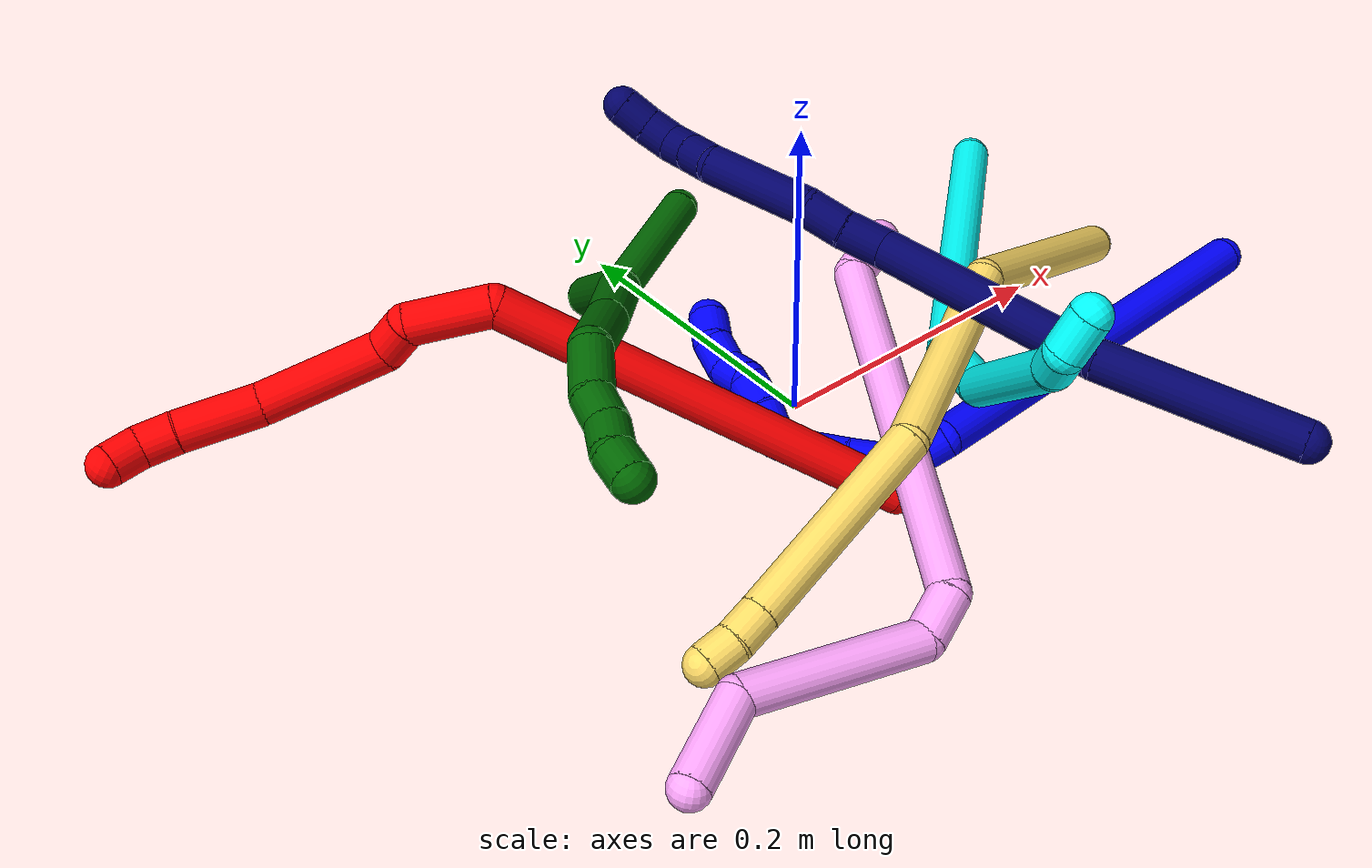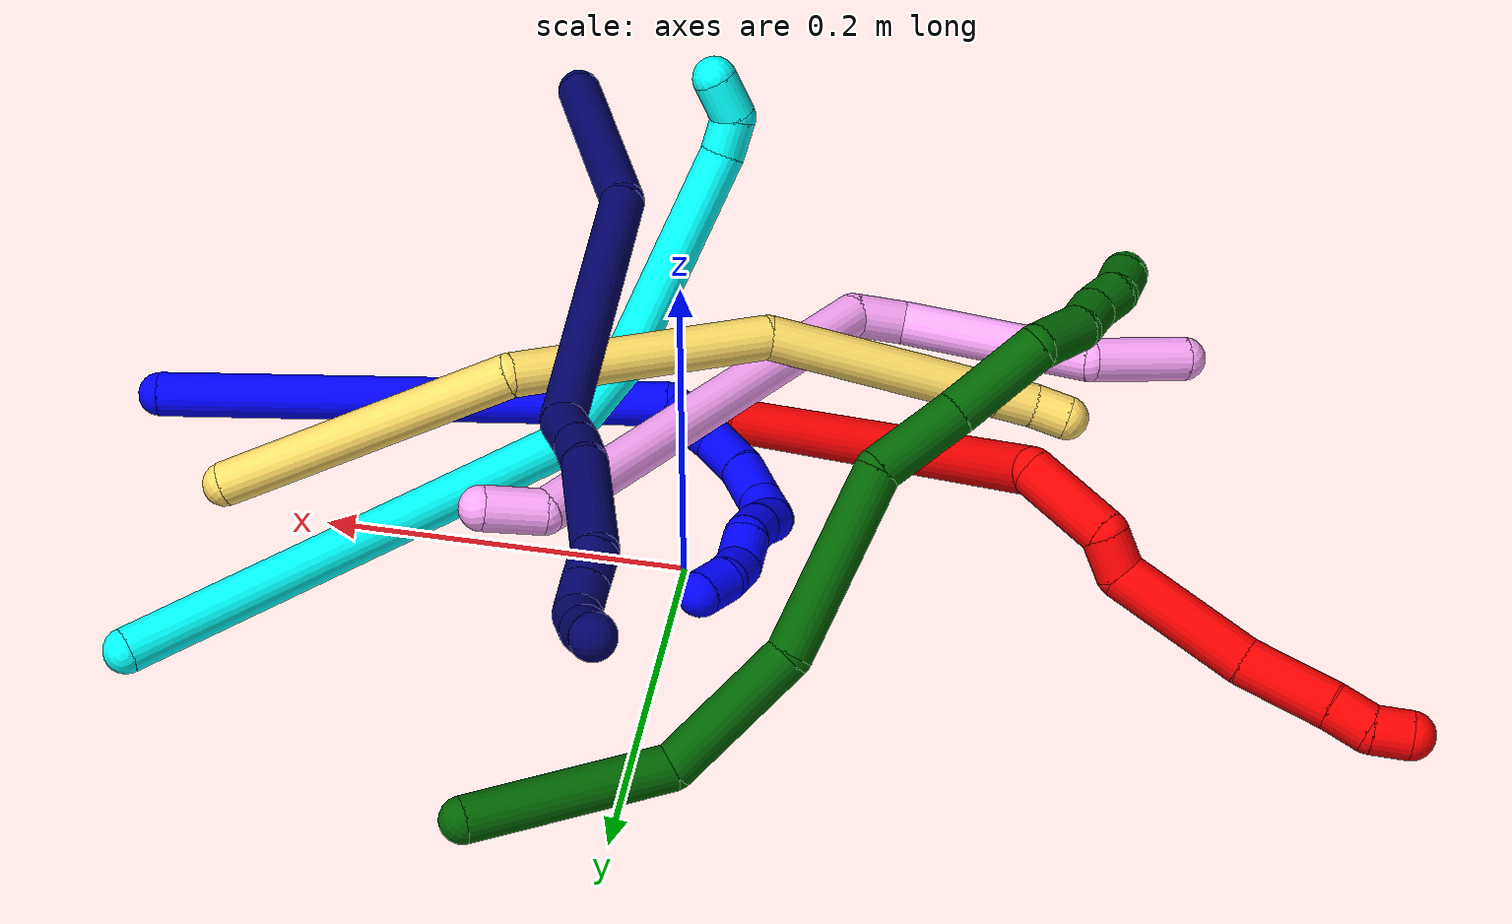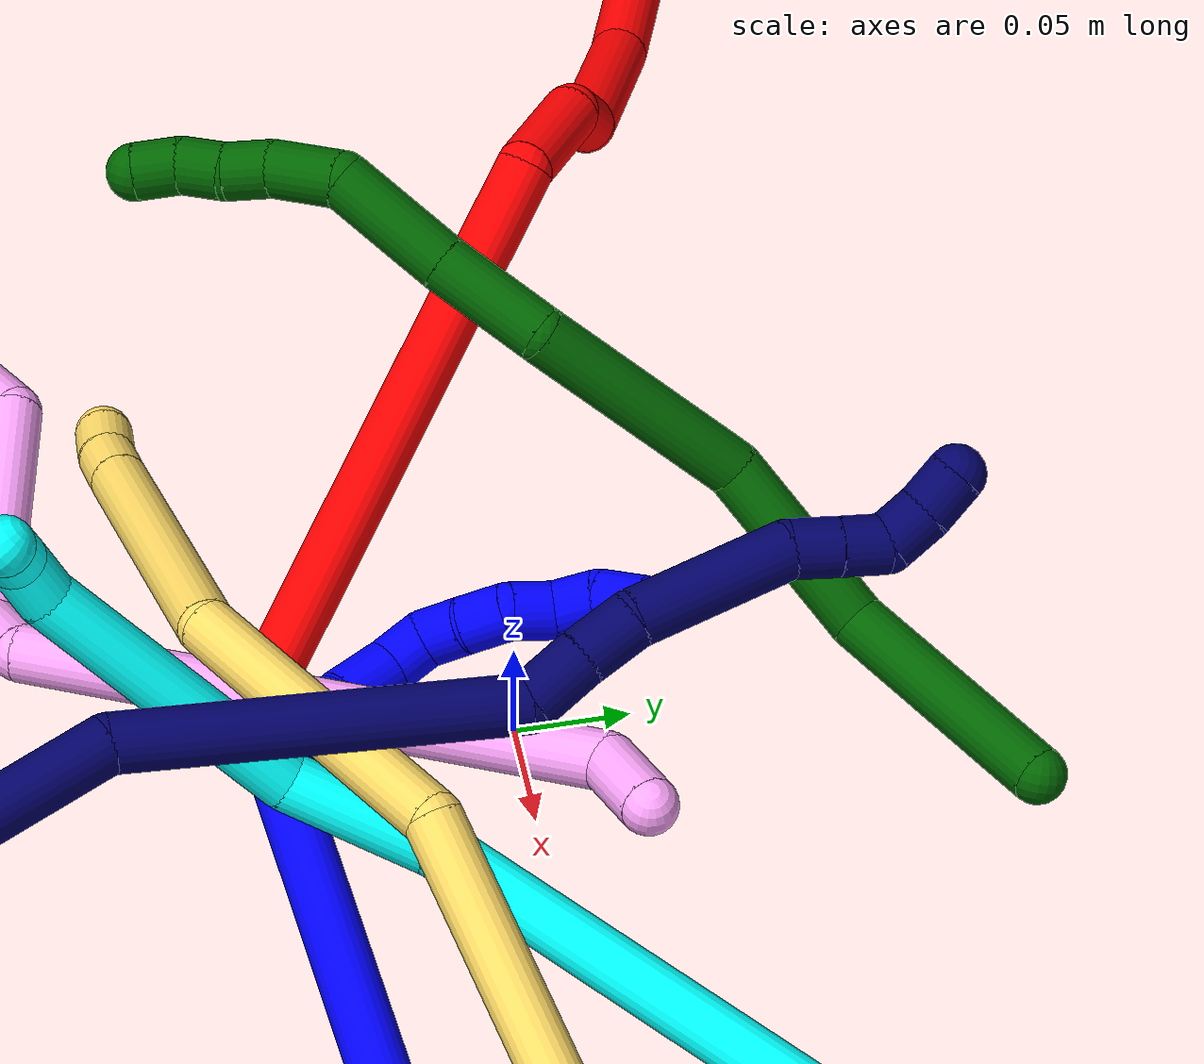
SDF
<sdf version="1.7">
 <world name="default">
  <plugin name="TubeGeneratorPlugin" filename="libtube_generator_plugin.so"/>
  <model name="photoneo_s_sensor">
   <static>1</static>
   <pose>0 0 2 1.57079 1.57079 3.14159</pose>
   <link name="link">
    <inertial><mass>0.1</mass></inertial>
    <sensor name="sensor" type="depth">
     <update_rate>30</update_rate>
     <camera>
      <horizontal_fov>1.22</horizontal_fov>
      <image><width>1920</width><height>1200</height><format>B8G8R8</format></image>
      <clip><near>0.1</near><far>4</far></clip>
      <depth_camera><output>points</output></depth_camera>
     </camera>
     <plugin name="camera_plugin" filename="libgazebo_ros_depth_camera.so">
      <baseline>0.2</baseline>
      <alwaysOn>1</alwaysOn>
      <updateRate>0.0</updateRate>
      <cameraName>camera_ir</cameraName>
      <imageTopicName>/camera/color/image_raw</imageTopicName>
      <cameraInfoTopicName>/camera/color/camera_info</cameraInfoTopicName>
      <depthImageTopicName>/camera/depth/image_raw</depthImageTopicName>
      <depthImageCameraInfoTopicName>/camera/depth/camera_info</depthImageCameraInfoTopicName>
      <pointCloudTopicName>/camera/depth/points</pointCloudTopicName>
      <frameName>fr_optical</frameName>
      <pointCloudCutoff>0.1</pointCloudCutoff>
      <pointCloudCutoffMax>2.0</pointCloudCutoffMax>
      <distortionK1>0</distortionK1>
      <distortionK2>0</distortionK2>
      <distortionK3>0</distortionK3>
      <distortionT1>0</distortionT1>
      <distortionT2>0</distortionT2>
      <CxPrime>0</CxPrime>
      <Cx>0</Cx>
      <Cy>0</Cy>
      <focalLength>0</focalLength>
      <hackBaseline>0</hackBaseline>
     </plugin>
    </sensor>
   </link>
  </model>
  <gravity>0 0 -9.8</gravity>
  <magnetic_field>6e-06 2.3e-05 -4.2e-05</magnetic_field>
  <atmosphere type="adiabatic"/>
  <physics name="default_physics" default="0" type="ode">
   <max_step_size>0.003</max_step_size>
   <real_time_factor>1</real_time_factor>
   <real_time_update_rate>1000</real_time_update_rate>
   <max_contacts>10000</max_contacts>
   <ode>
    <solver>
     <type>quick</type>
     <iters>100</iters>
     <sor>1.3</sor>
     <use_dynamic_moi_rescaling>0</use_dynamic_moi_rescaling>
    </solver>
    <constraints>
     <contact_max_correcting_vel>0</contact_max_correcting_vel>
     <contact_surface_layer>0.001</contact_surface_layer>
     <cfm>0</cfm>
     <erp>0.2</erp>
    </constraints>
   </ode>
  </physics>
  <scene><ambient>0.4 0.4 0.4 1</ambient><background>0.7 0.7 0.7 1</background><shadows>0</shadows></scene>
  <audio><device>default</device></audio>
  <spherical_coordinates>
   <surface_model>EARTH_WGS84</surface_model>
   <latitude_deg>0</latitude_deg>
   <longitude_deg>0</longitude_deg>
   <elevation>0</elevation>
   <heading_deg>0</heading_deg>
  </spherical_coordinates>
  <model name="bin">
   <static>1</static>
   <link name="bottom">
    <collision name="collision-bottom">
     <pose>0 0 -0.01 0 -0 0</pose>
     <geometry><box><size>0.8 0.6 0.02</size></box></geometry>
     <surface>
      <friction><ode><mu>100</mu><mu2>100</mu2></ode></friction>
      <contact><collide_bitmask>65535</collide_bitmask></contact>
     </surface>
    </collision>
   </link>
   <link name="west_wall">
    <collision name="collision-west_wall">
     <pose>-0.41 0 0.1 0 -0 0</pose>
     <geometry><box><size>0.02 0.6 0.2</size></box></geometry>
     <surface>
      <friction><ode><mu>100</mu><mu2>100</mu2></ode></friction>
      <contact><collide_bitmask>65535</collide_bitmask></contact>
     </surface>
    </collision>
   </link>
   <link name="east_wall">
    <collision name="collision-east_wall">
     <pose>0.41 0 0.1 0 -0 0</pose>
     <geometry><box><size>0.02 0.6 0.2</size></box></geometry>
     <surface>
      <friction><ode><mu>100</mu><mu2>100</mu2></ode></friction>
      <contact><collide_bitmask>65535</collide_bitmask></contact>
     </surface>
    </collision>
   </link>
   <link name="south_wall">
    <collision name="collision-south_wall">
     <pose>0 -0.31 0.1 0 -0 0</pose>
     <geometry><box><size>0.8 0.02 0.2</size></box></geometry>
     <surface>
      <friction><ode><mu>100</mu><mu2>100</mu2></ode></friction>
      <contact><collide_bitmask>65535</collide_bitmask></contact>
     </surface>
    </collision>
   </link>
   <link name="north_wall">
    <collision name="collision-north_wall">
     <pose>0 0.31 0.1 0 -0 0</pose>
     <geometry><box><size>0.8 0.02 0.2</size></box></geometry>
     <surface>
      <friction><ode><mu>100</mu><mu2>100</mu2></ode></friction>
      <contact><collide_bitmask>65535</collide_bitmask></contact>
     </surface>
    </collision>
   </link>
  </model>
  <model name="1">
   <static>0</static>
   <link name="1">
    <collision name="collision-cylinder-e_1_1_4">
     <pose>-0.132751 -0.024175 0.053975 0.421101 -1.15168 -0.275749</pose>
     <geometry><cylinder><radius>0.0125</radius><length>0.290659</length></cylinder></geometry>
     <surface>
      <friction><ode><mu>1.16</mu><mu2>1.16</mu2><slip1>0</slip1><slip2>0</slip2></ode></friction>
      <contact><ode><kp>1e+06</kp><kd>1</kd><max_vel>0</max_vel><min_depth>0.001</min_depth></ode></contact>
     </surface>
    </collision>
    <visual name="visual-cylinder-e_1_1_4">
     <pose>-0.132751 -0.024175 0.053975 0.421101 -1.15168 -0.275749</pose>
     <geometry><cylinder><radius>0.0125</radius><length>0.290659</length></cylinder></geometry>
     <material><ambient>0 0 1 1</ambient></material>
    </visual>
    <collision name="collision-cylinder-e_2_4_5">
     <pose>-0.278206 -0.040767 0.114553 -0.854375 -0.901256 0.433577</pose>
     <geometry><cylinder><radius>0.0125</radius><length>0.032402</length></cylinder></geometry>
     <surface>
      <friction><ode><mu>1.16</mu><mu2>1.16</mu2><slip1>0</slip1><slip2>0</slip2></ode></friction>
      <contact><ode><kp>1e+06</kp><kd>1</kd><max_vel>0</max_vel><min_depth>0.001</min_depth></ode></contact>
     </surface>
    </collision>
    <visual name="visual-cylinder-e_2_4_5">
     <pose>-0.278206 -0.040767 0.114553 -0.854375 -0.901256 0.433577</pose>
     <geometry><cylinder><radius>0.0125</radius><length>0.032402</length></cylinder></geometry>
     <material><ambient>0 0 1 1</ambient></material>
    </visual>
    <collision name="collision-cylinder-e_3_5_6">
     <pose>-0.296233 -0.028298 0.134422 -0.352922 -0.360136 0.064898</pose>
     <geometry><cylinder><radius>0.0125</radius><length>0.030214</length></cylinder></geometry>
     <surface>
      <friction><ode><mu>1.16</mu><mu2>1.16</mu2><slip1>0</slip1><slip2>0</slip2></ode></friction>
      <contact><ode><kp>1e+06</kp><kd>1</kd><max_vel>0</max_vel><min_depth>0.001</min_depth></ode></contact>
     </surface>
    </collision>
    <visual name="visual-cylinder-e_3_5_6">
     <pose>-0.296233 -0.028298 0.134422 -0.352922 -0.360136 0.064898</pose>
     <geometry><cylinder><radius>0.0125</radius><length>0.030214</length></cylinder></geometry>
     <material><ambient>0 0 1 1</ambient></material>
    </visual>
    <collision name="collision-cylinder-e_4_6_7">
     <pose>-0.304588 -0.017132 0.158942 -0.508985 -0.231061 0.060357</pose>
     <geometry><cylinder><radius>0.0125</radius><length>0.026478</length></cylinder></geometry>
     <surface>
      <friction><ode><mu>1.16</mu><mu2>1.16</mu2><slip1>0</slip1><slip2>0</slip2></ode></friction>
      <contact><ode><kp>1e+06</kp><kd>1</kd><max_vel>0</max_vel><min_depth>0.001</min_depth></ode></contact>
     </surface>
    </collision>
    <visual name="visual-cylinder-e_4_6_7">
     <pose>-0.304588 -0.017132 0.158942 -0.508985 -0.231061 0.060357</pose>
     <geometry><cylinder><radius>0.0125</radius><length>0.026478</length></cylinder></geometry>
     <material><ambient>0 0 1 1</ambient></material>
    </visual>
    <collision name="collision-cylinder-e_5_7_8">
     <pose>-0.308412 -0.007936 0.179829 -0.293901 -0.078516 0.011628</pose>
     <geometry><cylinder><radius>0.0125</radius><length>0.020192</length></cylinder></geometry>
     <surface>
      <friction><ode><mu>1.16</mu><mu2>1.16</mu2><slip1>0</slip1><slip2>0</slip2></ode></friction>
      <contact><ode><kp>1e+06</kp><kd>1</kd><max_vel>0</max_vel><min_depth>0.001</min_depth></ode></contact>
     </surface>
    </collision>
    <visual name="visual-cylinder-e_5_7_8">
     <pose>-0.308412 -0.007936 0.179829 -0.293901 -0.078516 0.011628</pose>
     <geometry><cylinder><radius>0.0125</radius><length>0.020192</length></cylinder></geometry>
     <material><ambient>0 0 1 1</ambient></material>
    </visual>
    <collision name="collision-cylinder-e_6_8_9">
     <pose>-0.30292 -0.004385 0.197247 -0.08153 0.677472 -0.028738</pose>
     <geometry><cylinder><radius>0.0125</radius><length>0.020049</length></cylinder></geometry>
     <surface>
      <friction><ode><mu>1.16</mu><mu2>1.16</mu2><slip1>0</slip1><slip2>0</slip2></ode></friction>
      <contact><ode><kp>1e+06</kp><kd>1</kd><max_vel>0</max_vel><min_depth>0.001</min_depth></ode></contact>
     </surface>
    </collision>
    <visual name="visual-cylinder-e_6_8_9">
     <pose>-0.30292 -0.004385 0.197247 -0.08153 0.677472 -0.028738</pose>
     <geometry><cylinder><radius>0.0125</radius><length>0.020049</length></cylinder></geometry>
     <material><ambient>0 0 1 1</ambient></material>
    </visual>
    <collision name="collision-cylinder-e_7_9_10">
     <pose>-0.291302 -0.001792 0.213264 -0.233303 0.562512 -0.067686</pose>
     <geometry><cylinder><radius>0.0125</radius><length>0.020006</length></cylinder></geometry>
     <surface>
      <friction><ode><mu>1.16</mu><mu2>1.16</mu2><slip1>0</slip1><slip2>0</slip2></ode></friction>
      <contact><ode><kp>1e+06</kp><kd>1</kd><max_vel>0</max_vel><min_depth>0.001</min_depth></ode></contact>
     </surface>
    </collision>
    <visual name="visual-cylinder-e_7_9_10">
     <pose>-0.291302 -0.001792 0.213264 -0.233303 0.562512 -0.067686</pose>
     <geometry><cylinder><radius>0.0125</radius><length>0.020006</length></cylinder></geometry>
     <material><ambient>0 0 1 1</ambient></material>
    </visual>
    <collision name="collision-cylinder-e_8_10_11">
     <pose>-0.283 0.006992 0.228174 -0.796558 0.301275 -0.12756</pose>
     <geometry><cylinder><radius>0.0125</radius><length>0.02</length></cylinder></geometry>
     <surface>
      <friction><ode><mu>1.16</mu><mu2>1.16</mu2><slip1>0</slip1><slip2>0</slip2></ode></friction>
      <contact><ode><kp>1e+06</kp><kd>1</kd><max_vel>0</max_vel><min_depth>0.001</min_depth></ode></contact>
     </surface>
    </collision>
    <visual name="visual-cylinder-e_8_10_11">
     <pose>-0.283 0.006992 0.228174 -0.796558 0.301275 -0.12756</pose>
     <geometry><cylinder><radius>0.0125</radius><length>0.02</length></cylinder></geometry>
     <material><ambient>0 0 1 1</ambient></material>
    </visual>
    <collision name="collision-cylinder-e_9_11_12">
     <pose>-0.274444 0.015994 0.242853 -0.265373 0.592956 -0.0815</pose>
     <geometry><cylinder><radius>0.0125</radius><length>0.02</length></cylinder></geometry>
     <surface>
      <friction><ode><mu>1.16</mu><mu2>1.16</mu2><slip1>0</slip1><slip2>0</slip2></ode></friction>
      <contact><ode><kp>1e+06</kp><kd>1</kd><max_vel>0</max_vel><min_depth>0.001</min_depth></ode></contact>
     </surface>
    </collision>
    <visual name="visual-cylinder-e_9_11_12">
     <pose>-0.274444 0.015994 0.242853 -0.265373 0.592956 -0.0815</pose>
     <geometry><cylinder><radius>0.0125</radius><length>0.02</length></cylinder></geometry>
     <material><ambient>0 0 1 1</ambient></material>
    </visual>
    <collision name="collision-cylinder-e_10_12_2">
     <pose>-0.261043 0.021848 0.255899 -0.630177 0.896648 -0.311023</pose>
     <geometry><cylinder><radius>0.0125</radius><length>0.02</length></cylinder></geometry>
     <surface>
      <friction><ode><mu>1.16</mu><mu2>1.16</mu2><slip1>0</slip1><slip2>0</slip2></ode></friction>
      <contact><ode><kp>1e+06</kp><kd>1</kd><max_vel>0</max_vel><min_depth>0.001</min_depth></ode></contact>
     </surface>
    </collision>
    <visual name="visual-cylinder-e_10_12_2">
     <pose>-0.261043 0.021848 0.255899 -0.630177 0.896648 -0.311023</pose>
     <geometry><cylinder><radius>0.0125</radius><length>0.02</length></cylinder></geometry>
     <material><ambient>0 0 1 1</ambient></material>
    </visual>
    <collision name="collision-sphere-2">
     <pose>-0.253231 0.025526 0.260943 0 -0 0</pose>
     <geometry><sphere><radius>0.0125</radius></sphere></geometry>
     <surface>
      <friction><ode><mu>1.16</mu><mu2>1.16</mu2><slip1>0</slip1><slip2>0</slip2></ode></friction>
      <contact><ode><kp>1e+06</kp><kd>1</kd><max_vel>0</max_vel><min_depth>0.001</min_depth></ode></contact>
     </surface>
    </collision>
    <visual name="visual-sphere-2">
     <pose>-0.253231 0.025526 0.260943 0 -0 0</pose>
     <geometry><sphere><radius>0.0125</radius></sphere></geometry>
     <material><ambient>0 0 1 1</ambient></material>
    </visual>
    <collision name="collision-sphere-12">
     <pose>-0.268856 0.018169 0.250856 0 -0 0</pose>
     <geometry><sphere><radius>0.0125</radius></sphere></geometry>
     <surface>
      <friction><ode><mu>1.16</mu><mu2>1.16</mu2><slip1>0</slip1><slip2>0</slip2></ode></friction>
      <contact><ode><kp>1e+06</kp><kd>1</kd><max_vel>0</max_vel><min_depth>0.001</min_depth></ode></contact>
     </surface>
    </collision>
    <visual name="visual-sphere-12">
     <pose>-0.268856 0.018169 0.250856 0 -0 0</pose>
     <geometry><sphere><radius>0.0125</radius></sphere></geometry>
     <material><ambient>0 0 1 1</ambient></material>
    </visual>
    <collision name="collision-sphere-11">
     <pose>-0.280032 0.013819 0.23485 0 -0 0</pose>
     <geometry><sphere><radius>0.0125</radius></sphere></geometry>
     <surface>
      <friction><ode><mu>1.16</mu><mu2>1.16</mu2><slip1>0</slip1><slip2>0</slip2></ode></friction>
      <contact><ode><kp>1e+06</kp><kd>1</kd><max_vel>0</max_vel><min_depth>0.001</min_depth></ode></contact>
     </surface>
    </collision>
    <visual name="visual-sphere-11">
     <pose>-0.280032 0.013819 0.23485 0 -0 0</pose>
     <geometry><sphere><radius>0.0125</radius></sphere></geometry>
     <material><ambient>0 0 1 1</ambient></material>
    </visual>
    <collision name="collision-sphere-10">
     <pose>-0.285967 0.000164 0.221497 0 -0 0</pose>
     <geometry><sphere><radius>0.0125</radius></sphere></geometry>
     <surface>
      <friction><ode><mu>1.16</mu><mu2>1.16</mu2><slip1>0</slip1><slip2>0</slip2></ode></friction>
      <contact><ode><kp>1e+06</kp><kd>1</kd><max_vel>0</max_vel><min_depth>0.001</min_depth></ode></contact>
     </surface>
    </collision>
    <visual name="visual-sphere-10">
     <pose>-0.285967 0.000164 0.221497 0 -0 0</pose>
     <geometry><sphere><radius>0.0125</radius></sphere></geometry>
     <material><ambient>0 0 1 1</ambient></material>
    </visual>
    <collision name="collision-sphere-9">
     <pose>-0.296637 -0.003748 0.205032 0 -0 0</pose>
     <geometry><sphere><radius>0.0125</radius></sphere></geometry>
     <surface>
      <friction><ode><mu>1.16</mu><mu2>1.16</mu2><slip1>0</slip1><slip2>0</slip2></ode></friction>
      <contact><ode><kp>1e+06</kp><kd>1</kd><max_vel>0</max_vel><min_depth>0.001</min_depth></ode></contact>
     </surface>
    </collision>
    <visual name="visual-sphere-9">
     <pose>-0.296637 -0.003748 0.205032 0 -0 0</pose>
     <geometry><sphere><radius>0.0125</radius></sphere></geometry>
     <material><ambient>0 0 1 1</ambient></material>
    </visual>
    <collision name="collision-sphere-4">
     <pose>-0.265503 -0.04835 0.10795 0 -0 0</pose>
     <geometry><sphere><radius>0.0125</radius></sphere></geometry>
     <surface>
      <friction><ode><mu>1.16</mu><mu2>1.16</mu2><slip1>0</slip1><slip2>0</slip2></ode></friction>
      <contact><ode><kp>1e+06</kp><kd>1</kd><max_vel>0</max_vel><min_depth>0.001</min_depth></ode></contact>
     </surface>
    </collision>
    <visual name="visual-sphere-4">
     <pose>-0.265503 -0.04835 0.10795 0 -0 0</pose>
     <geometry><sphere><radius>0.0125</radius></sphere></geometry>
     <material><ambient>0 0 1 1</ambient></material>
    </visual>
    <collision name="collision-sphere-1">
     <geometry><sphere><radius>0.0125</radius></sphere></geometry>
     <surface>
      <friction><ode><mu>1.16</mu><mu2>1.16</mu2><slip1>0</slip1><slip2>0</slip2></ode></friction>
      <contact><ode><kp>1e+06</kp><kd>1</kd><max_vel>0</max_vel><min_depth>0.001</min_depth></ode></contact>
     </surface>
    </collision>
    <visual name="visual-sphere-1">
     <geometry><sphere><radius>0.0125</radius></sphere></geometry>
     <material><ambient>0 0 1 1</ambient></material>
    </visual>
    <collision name="collision-sphere-8">
     <pose>-0.309204 -0.005021 0.189462 0 -0 0</pose>
     <geometry><sphere><radius>0.0125</radius></sphere></geometry>
     <surface>
      <friction><ode><mu>1.16</mu><mu2>1.16</mu2><slip1>0</slip1><slip2>0</slip2></ode></friction>
      <contact><ode><kp>1e+06</kp><kd>1</kd><max_vel>0</max_vel><min_depth>0.001</min_depth></ode></contact>
     </surface>
    </collision>
    <visual name="visual-sphere-8">
     <pose>-0.309204 -0.005021 0.189462 0 -0 0</pose>
     <geometry><sphere><radius>0.0125</radius></sphere></geometry>
     <material><ambient>0 0 1 1</ambient></material>
    </visual>
    <collision name="collision-sphere-5">
     <pose>-0.290909 -0.033185 0.121156 0 -0 0</pose>
     <geometry><sphere><radius>0.0125</radius></sphere></geometry>
     <surface>
      <friction><ode><mu>1.16</mu><mu2>1.16</mu2><slip1>0</slip1><slip2>0</slip2></ode></friction>
      <contact><ode><kp>1e+06</kp><kd>1</kd><max_vel>0</max_vel><min_depth>0.001</min_depth></ode></contact>
     </surface>
    </collision>
    <visual name="visual-sphere-5">
     <pose>-0.290909 -0.033185 0.121156 0 -0 0</pose>
     <geometry><sphere><radius>0.0125</radius></sphere></geometry>
     <material><ambient>0 0 1 1</ambient></material>
    </visual>
    <collision name="collision-sphere-6">
     <pose>-0.301556 -0.023411 0.147689 0 -0 0</pose>
     <geometry><sphere><radius>0.0125</radius></sphere></geometry>
     <surface>
      <friction><ode><mu>1.16</mu><mu2>1.16</mu2><slip1>0</slip1><slip2>0</slip2></ode></friction>
      <contact><ode><kp>1e+06</kp><kd>1</kd><max_vel>0</max_vel><min_depth>0.001</min_depth></ode></contact>
     </surface>
    </collision>
    <visual name="visual-sphere-6">
     <pose>-0.301556 -0.023411 0.147689 0 -0 0</pose>
     <geometry><sphere><radius>0.0125</radius></sphere></geometry>
     <material><ambient>0 0 1 1</ambient></material>
    </visual>
    <collision name="collision-sphere-7">
     <pose>-0.30762 -0.010852 0.170196 0 -0 0</pose>
     <geometry><sphere><radius>0.0125</radius></sphere></geometry>
     <surface>
      <friction><ode><mu>1.16</mu><mu2>1.16</mu2><slip1>0</slip1><slip2>0</slip2></ode></friction>
      <contact><ode><kp>1e+06</kp><kd>1</kd><max_vel>0</max_vel><min_depth>0.001</min_depth></ode></contact>
     </surface>
    </collision>
    <visual name="visual-sphere-7">
     <pose>-0.30762 -0.010852 0.170196 0 -0 0</pose>
     <geometry><sphere><radius>0.0125</radius></sphere></geometry>
     <material><ambient>0 0 1 1</ambient></material>
    </visual>
    <inertial>
     <pose>-0.198227 -0.018087 0.108122 0 -0 0</pose>
     <mass>0.5</mass>
     <inertia>
      <ixx>0.000574</ixx>
      <ixy>0</ixy>
      <ixz>0</ixz>
      <iyy>0.001808</iyy>
      <iyz>0</iyz>
      <izz>0.002236</izz>
     </inertia>
    </inertial>
   </link>
   <pose>0.317229 -0.073567 0.011499 -1.0268 -0.303483 0.334996</pose>
  </model>
  <model name="2">
   <static>0</static>
   <link name="2">
    <collision name="collision-cylinder-e_1_1_4">
     <pose>0.002095 0.003672 0.131326 -0.027955 0.015947 -0.000223</pose>
     <geometry><cylinder><radius>0.0125</radius><length>0.262789</length></cylinder></geometry>
     <surface>
      <friction><ode><mu>1.16</mu><mu2>1.16</mu2><slip1>0</slip1><slip2>0</slip2></ode></friction>
      <contact><ode><kp>1e+06</kp><kd>1</kd><max_vel>0</max_vel><min_depth>0.001</min_depth></ode></contact>
     </surface>
    </collision>
    <visual name="visual-cylinder-e_1_1_4">
     <pose>0.002095 0.003672 0.131326 -0.027955 0.015947 -0.000223</pose>
     <geometry><cylinder><radius>0.0125</radius><length>0.262789</length></cylinder></geometry>
     <material><ambient>1 0 0 1</ambient></material>
    </visual>
    <collision name="collision-cylinder-e_2_4_5">
     <pose>-0.009186 0.017567 0.281115 -0.505676 -0.564937 0.149691</pose>
     <geometry><cylinder><radius>0.0125</radius><length>0.049973</length></cylinder></geometry>
     <surface>
      <friction><ode><mu>1.16</mu><mu2>1.16</mu2><slip1>0</slip1><slip2>0</slip2></ode></friction>
      <contact><ode><kp>1e+06</kp><kd>1</kd><max_vel>0</max_vel><min_depth>0.001</min_depth></ode></contact>
     </surface>
    </collision>
    <visual name="visual-cylinder-e_2_4_5">
     <pose>-0.009186 0.017567 0.281115 -0.505676 -0.564937 0.149691</pose>
     <geometry><cylinder><radius>0.0125</radius><length>0.049973</length></cylinder></geometry>
     <material><ambient>1 0 0 1</ambient></material>
    </visual>
    <collision name="collision-cylinder-e_3_5_6">
     <pose>-0.030309 0.035781 0.300896 -1.40737 -0.763167 0.65638</pose>
     <geometry><cylinder><radius>0.0125</radius><length>0.022414</length></cylinder></geometry>
     <surface>
      <friction><ode><mu>1.16</mu><mu2>1.16</mu2><slip1>0</slip1><slip2>0</slip2></ode></friction>
      <contact><ode><kp>1e+06</kp><kd>1</kd><max_vel>0</max_vel><min_depth>0.001</min_depth></ode></contact>
     </surface>
    </collision>
    <visual name="visual-cylinder-e_3_5_6">
     <pose>-0.030309 0.035781 0.300896 -1.40737 -0.763167 0.65638</pose>
     <geometry><cylinder><radius>0.0125</radius><length>0.022414</length></cylinder></geometry>
     <material><ambient>1 0 0 1</ambient></material>
    </visual>
    <collision name="collision-cylinder-e_4_6_7">
     <pose>-0.064337 0.05533 0.326108 -0.450535 -0.780441 0.187955</pose>
     <geometry><cylinder><radius>0.0125</radius><length>0.074706</length></cylinder></geometry>
     <surface>
      <friction><ode><mu>1.16</mu><mu2>1.16</mu2><slip1>0</slip1><slip2>0</slip2></ode></friction>
      <contact><ode><kp>1e+06</kp><kd>1</kd><max_vel>0</max_vel><min_depth>0.001</min_depth></ode></contact>
     </surface>
    </collision>
    <visual name="visual-cylinder-e_4_6_7">
     <pose>-0.064337 0.05533 0.326108 -0.450535 -0.780441 0.187955</pose>
     <geometry><cylinder><radius>0.0125</radius><length>0.074706</length></cylinder></geometry>
     <material><ambient>1 0 0 1</ambient></material>
    </visual>
    <collision name="collision-cylinder-e_5_7_8">
     <pose>-0.10648 0.071139 0.367722 -0.235461 -0.716264 0.088478</pose>
     <geometry><cylinder><radius>0.0125</radius><length>0.048317</length></cylinder></geometry>
     <surface>
      <friction><ode><mu>1.16</mu><mu2>1.16</mu2><slip1>0</slip1><slip2>0</slip2></ode></friction>
      <contact><ode><kp>1e+06</kp><kd>1</kd><max_vel>0</max_vel><min_depth>0.001</min_depth></ode></contact>
     </surface>
    </collision>
    <visual name="visual-cylinder-e_5_7_8">
     <pose>-0.10648 0.071139 0.367722 -0.235461 -0.716264 0.088478</pose>
     <geometry><cylinder><radius>0.0125</radius><length>0.048317</length></cylinder></geometry>
     <material><ambient>1 0 0 1</ambient></material>
    </visual>
    <collision name="collision-cylinder-e_6_8_9">
     <pose>-0.129898 0.078069 0.392782 -0.349966 -0.768573 0.142743</pose>
     <geometry><cylinder><radius>0.0125</radius><length>0.021742</length></cylinder></geometry>
     <surface>
      <friction><ode><mu>1.16</mu><mu2>1.16</mu2><slip1>0</slip1><slip2>0</slip2></ode></friction>
      <contact><ode><kp>1e+06</kp><kd>1</kd><max_vel>0</max_vel><min_depth>0.001</min_depth></ode></contact>
     </surface>
    </collision>
    <visual name="visual-cylinder-e_6_8_9">
     <pose>-0.129898 0.078069 0.392782 -0.349966 -0.768573 0.142743</pose>
     <geometry><cylinder><radius>0.0125</radius><length>0.021742</length></cylinder></geometry>
     <material><ambient>1 0 0 1</ambient></material>
    </visual>
    <collision name="collision-cylinder-e_7_9_2">
     <pose>-0.14535 0.079086 0.406082 0.272079 -0.906123 -0.133084</pose>
     <geometry><cylinder><radius>0.0125</radius><length>0.02006</length></cylinder></geometry>
     <surface>
      <friction><ode><mu>1.16</mu><mu2>1.16</mu2><slip1>0</slip1><slip2>0</slip2></ode></friction>
      <contact><ode><kp>1e+06</kp><kd>1</kd><max_vel>0</max_vel><min_depth>0.001</min_depth></ode></contact>
     </surface>
    </collision>
    <visual name="visual-cylinder-e_7_9_2">
     <pose>-0.14535 0.079086 0.406082 0.272079 -0.906123 -0.133084</pose>
     <geometry><cylinder><radius>0.0125</radius><length>0.02006</length></cylinder></geometry>
     <material><ambient>1 0 0 1</ambient></material>
    </visual>
    <collision name="collision-sphere-2">
     <pose>-0.153244 0.077424 0.412041 0 -0 0</pose>
     <geometry><sphere><radius>0.0125</radius></sphere></geometry>
     <surface>
      <friction><ode><mu>1.16</mu><mu2>1.16</mu2><slip1>0</slip1><slip2>0</slip2></ode></friction>
      <contact><ode><kp>1e+06</kp><kd>1</kd><max_vel>0</max_vel><min_depth>0.001</min_depth></ode></contact>
     </surface>
    </collision>
    <visual name="visual-sphere-2">
     <pose>-0.153244 0.077424 0.412041 0 -0 0</pose>
     <geometry><sphere><radius>0.0125</radius></sphere></geometry>
     <material><ambient>1 0 0 1</ambient></material>
    </visual>
    <collision name="collision-sphere-9">
     <pose>-0.137455 0.080749 0.400123 0 -0 0</pose>
     <geometry><sphere><radius>0.0125</radius></sphere></geometry>
     <surface>
      <friction><ode><mu>1.16</mu><mu2>1.16</mu2><slip1>0</slip1><slip2>0</slip2></ode></friction>
      <contact><ode><kp>1e+06</kp><kd>1</kd><max_vel>0</max_vel><min_depth>0.001</min_depth></ode></contact>
     </surface>
    </collision>
    <visual name="visual-sphere-9">
     <pose>-0.137455 0.080749 0.400123 0 -0 0</pose>
     <geometry><sphere><radius>0.0125</radius></sphere></geometry>
     <material><ambient>1 0 0 1</ambient></material>
    </visual>
    <collision name="collision-sphere-4">
     <pose>0.004191 0.007344 0.262653 0 -0 0</pose>
     <geometry><sphere><radius>0.0125</radius></sphere></geometry>
     <surface>
      <friction><ode><mu>1.16</mu><mu2>1.16</mu2><slip1>0</slip1><slip2>0</slip2></ode></friction>
      <contact><ode><kp>1e+06</kp><kd>1</kd><max_vel>0</max_vel><min_depth>0.001</min_depth></ode></contact>
     </surface>
    </collision>
    <visual name="visual-sphere-4">
     <pose>0.004191 0.007344 0.262653 0 -0 0</pose>
     <geometry><sphere><radius>0.0125</radius></sphere></geometry>
     <material><ambient>1 0 0 1</ambient></material>
    </visual>
    <collision name="collision-sphere-1">
     <geometry><sphere><radius>0.0125</radius></sphere></geometry>
     <surface>
      <friction><ode><mu>1.16</mu><mu2>1.16</mu2><slip1>0</slip1><slip2>0</slip2></ode></friction>
      <contact><ode><kp>1e+06</kp><kd>1</kd><max_vel>0</max_vel><min_depth>0.001</min_depth></ode></contact>
     </surface>
    </collision>
    <visual name="visual-sphere-1">
     <geometry><sphere><radius>0.0125</radius></sphere></geometry>
     <material><ambient>1 0 0 1</ambient></material>
    </visual>
    <collision name="collision-sphere-8">
     <pose>-0.122342 0.07539 0.38544 0 -0 0</pose>
     <geometry><sphere><radius>0.0125</radius></sphere></geometry>
     <surface>
      <friction><ode><mu>1.16</mu><mu2>1.16</mu2><slip1>0</slip1><slip2>0</slip2></ode></friction>
      <contact><ode><kp>1e+06</kp><kd>1</kd><max_vel>0</max_vel><min_depth>0.001</min_depth></ode></contact>
     </surface>
    </collision>
    <visual name="visual-sphere-8">
     <pose>-0.122342 0.07539 0.38544 0 -0 0</pose>
     <geometry><sphere><radius>0.0125</radius></sphere></geometry>
     <material><ambient>1 0 0 1</ambient></material>
    </visual>
    <collision name="collision-sphere-5">
     <pose>-0.022563 0.02779 0.299578 0 -0 0</pose>
     <geometry><sphere><radius>0.0125</radius></sphere></geometry>
     <surface>
      <friction><ode><mu>1.16</mu><mu2>1.16</mu2><slip1>0</slip1><slip2>0</slip2></ode></friction>
      <contact><ode><kp>1e+06</kp><kd>1</kd><max_vel>0</max_vel><min_depth>0.001</min_depth></ode></contact>
     </surface>
    </collision>
    <visual name="visual-sphere-5">
     <pose>-0.022563 0.02779 0.299578 0 -0 0</pose>
     <geometry><sphere><radius>0.0125</radius></sphere></geometry>
     <material><ambient>1 0 0 1</ambient></material>
    </visual>
    <collision name="collision-sphere-6">
     <pose>-0.038056 0.043772 0.302214 0 -0 0</pose>
     <geometry><sphere><radius>0.0125</radius></sphere></geometry>
     <surface>
      <friction><ode><mu>1.16</mu><mu2>1.16</mu2><slip1>0</slip1><slip2>0</slip2></ode></friction>
      <contact><ode><kp>1e+06</kp><kd>1</kd><max_vel>0</max_vel><min_depth>0.001</min_depth></ode></contact>
     </surface>
    </collision>
    <visual name="visual-sphere-6">
     <pose>-0.038056 0.043772 0.302214 0 -0 0</pose>
     <geometry><sphere><radius>0.0125</radius></sphere></geometry>
     <material><ambient>1 0 0 1</ambient></material>
    </visual>
    <collision name="collision-sphere-7">
     <pose>-0.090618 0.066888 0.350003 0 -0 0</pose>
     <geometry><sphere><radius>0.0125</radius></sphere></geometry>
     <surface>
      <friction><ode><mu>1.16</mu><mu2>1.16</mu2><slip1>0</slip1><slip2>0</slip2></ode></friction>
      <contact><ode><kp>1e+06</kp><kd>1</kd><max_vel>0</max_vel><min_depth>0.001</min_depth></ode></contact>
     </surface>
    </collision>
    <visual name="visual-sphere-7">
     <pose>-0.090618 0.066888 0.350003 0 -0 0</pose>
     <geometry><sphere><radius>0.0125</radius></sphere></geometry>
     <material><ambient>1 0 0 1</ambient></material>
    </visual>
    <inertial>
     <pose>-0.032558 0.026999 0.228237 0 -0 0</pose>
     <mass>0.5</mass>
     <inertia>
      <ixx>0.001566</ixx>
      <ixy>0</ixy>
      <ixz>0</ixz>
      <iyy>0.001598</iyy>
      <iyz>0</iyz>
      <izz>-1.1e-05</izz>
     </inertia>
    </inertial>
   </link>
   <pose>-0.016627 -0.109858 0.011491 -0.868987 -0.664567 0.40523</pose>
  </model>
  <model name="3">
   <static>0</static>
   <link name="3">
    <collision name="collision-cylinder-e_1_1_4">
     <pose>-0.091901 -0.077048 -0.049959 2.14606 -0.785798 -1.30314</pose>
     <geometry><cylinder><radius>0.0125</radius><length>0.259832</length></cylinder></geometry>
     <surface>
      <friction><ode><mu>1.16</mu><mu2>1.16</mu2><slip1>0</slip1><slip2>0</slip2></ode></friction>
      <contact><ode><kp>1e+06</kp><kd>1</kd><max_vel>0</max_vel><min_depth>0.001</min_depth></ode></contact>
     </surface>
    </collision>
    <visual name="visual-cylinder-e_1_1_4">
     <pose>-0.091901 -0.077048 -0.049959 2.14606 -0.785798 -1.30314</pose>
     <geometry><cylinder><radius>0.0125</radius><length>0.259832</length></cylinder></geometry>
     <material><ambient>0.003922 1 0.996078 1</ambient></material>
    </visual>
    <collision name="collision-cylinder-e_2_4_5">
     <pose>-0.195738 -0.181163 -0.113716 2.0422 -0.374344 -0.599588</pose>
     <geometry><cylinder><radius>0.0125</radius><length>0.065282</length></cylinder></geometry>
     <surface>
      <friction><ode><mu>1.16</mu><mu2>1.16</mu2><slip1>0</slip1><slip2>0</slip2></ode></friction>
      <contact><ode><kp>1e+06</kp><kd>1</kd><max_vel>0</max_vel><min_depth>0.001</min_depth></ode></contact>
     </surface>
    </collision>
    <visual name="visual-cylinder-e_2_4_5">
     <pose>-0.195738 -0.181163 -0.113716 2.0422 -0.374344 -0.599588</pose>
     <geometry><cylinder><radius>0.0125</radius><length>0.065282</length></cylinder></geometry>
     <material><ambient>0.003922 1 0.996078 1</ambient></material>
    </visual>
    <collision name="collision-cylinder-e_3_5_6">
     <pose>-0.218154 -0.271271 -0.132957 1.65695 -0.164149 -0.178862</pose>
     <geometry><cylinder><radius>0.0125</radius><length>0.128275</length></cylinder></geometry>
     <surface>
      <friction><ode><mu>1.16</mu><mu2>1.16</mu2><slip1>0</slip1><slip2>0</slip2></ode></friction>
      <contact><ode><kp>1e+06</kp><kd>1</kd><max_vel>0</max_vel><min_depth>0.001</min_depth></ode></contact>
     </surface>
    </collision>
    <visual name="visual-cylinder-e_3_5_6">
     <pose>-0.218154 -0.271271 -0.132957 1.65695 -0.164149 -0.178862</pose>
     <geometry><cylinder><radius>0.0125</radius><length>0.128275</length></cylinder></geometry>
     <material><ambient>0.003922 1 0.996078 1</ambient></material>
    </visual>
    <collision name="collision-cylinder-e_4_6_7">
     <pose>-0.228964 -0.345013 -0.136251 1.37245 -0.030143 -0.024688</pose>
     <geometry><cylinder><radius>0.0125</radius><length>0.021841</length></cylinder></geometry>
     <surface>
      <friction><ode><mu>1.16</mu><mu2>1.16</mu2><slip1>0</slip1><slip2>0</slip2></ode></friction>
      <contact><ode><kp>1e+06</kp><kd>1</kd><max_vel>0</max_vel><min_depth>0.001</min_depth></ode></contact>
     </surface>
    </collision>
    <visual name="visual-cylinder-e_4_6_7">
     <pose>-0.228964 -0.345013 -0.136251 1.37245 -0.030143 -0.024688</pose>
     <geometry><cylinder><radius>0.0125</radius><length>0.021841</length></cylinder></geometry>
     <material><ambient>0.003922 1 0.996078 1</ambient></material>
    </visual>
    <collision name="collision-cylinder-e_5_7_2">
     <pose>-0.221511 -0.364468 -0.130075 1.13973 0.679452 0.445423</pose>
     <geometry><cylinder><radius>0.0125</radius><length>0.02477</length></cylinder></geometry>
     <surface>
      <friction><ode><mu>1.16</mu><mu2>1.16</mu2><slip1>0</slip1><slip2>0</slip2></ode></friction>
      <contact><ode><kp>1e+06</kp><kd>1</kd><max_vel>0</max_vel><min_depth>0.001</min_depth></ode></contact>
     </surface>
    </collision>
    <visual name="visual-cylinder-e_5_7_2">
     <pose>-0.221511 -0.364468 -0.130075 1.13973 0.679452 0.445423</pose>
     <geometry><cylinder><radius>0.0125</radius><length>0.02477</length></cylinder></geometry>
     <material><ambient>0.003922 1 0.996078 1</ambient></material>
    </visual>
    <collision name="collision-sphere-2">
     <pose>-0.213729 -0.373221 -0.126049 0 -0 0</pose>
     <geometry><sphere><radius>0.0125</radius></sphere></geometry>
     <surface>
      <friction><ode><mu>1.16</mu><mu2>1.16</mu2><slip1>0</slip1><slip2>0</slip2></ode></friction>
      <contact><ode><kp>1e+06</kp><kd>1</kd><max_vel>0</max_vel><min_depth>0.001</min_depth></ode></contact>
     </surface>
    </collision>
    <visual name="visual-sphere-2">
     <pose>-0.213729 -0.373221 -0.126049 0 -0 0</pose>
     <geometry><sphere><radius>0.0125</radius></sphere></geometry>
     <material><ambient>0.003922 1 0.996078 1</ambient></material>
    </visual>
    <collision name="collision-sphere-7">
     <pose>-0.229294 -0.355715 -0.1341 0 -0 0</pose>
     <geometry><sphere><radius>0.0125</radius></sphere></geometry>
     <surface>
      <friction><ode><mu>1.16</mu><mu2>1.16</mu2><slip1>0</slip1><slip2>0</slip2></ode></friction>
      <contact><ode><kp>1e+06</kp><kd>1</kd><max_vel>0</max_vel><min_depth>0.001</min_depth></ode></contact>
     </surface>
    </collision>
    <visual name="visual-sphere-7">
     <pose>-0.229294 -0.355715 -0.1341 0 -0 0</pose>
     <geometry><sphere><radius>0.0125</radius></sphere></geometry>
     <material><ambient>0.003922 1 0.996078 1</ambient></material>
    </visual>
    <collision name="collision-sphere-6">
     <pose>-0.228635 -0.334311 -0.138402 0 -0 0</pose>
     <geometry><sphere><radius>0.0125</radius></sphere></geometry>
     <surface>
      <friction><ode><mu>1.16</mu><mu2>1.16</mu2><slip1>0</slip1><slip2>0</slip2></ode></friction>
      <contact><ode><kp>1e+06</kp><kd>1</kd><max_vel>0</max_vel><min_depth>0.001</min_depth></ode></contact>
     </surface>
    </collision>
    <visual name="visual-sphere-6">
     <pose>-0.228635 -0.334311 -0.138402 0 -0 0</pose>
     <geometry><sphere><radius>0.0125</radius></sphere></geometry>
     <material><ambient>0.003922 1 0.996078 1</ambient></material>
    </visual>
    <collision name="collision-sphere-5">
     <pose>-0.207673 -0.20823 -0.127513 0 -0 0</pose>
     <geometry><sphere><radius>0.0125</radius></sphere></geometry>
     <surface>
      <friction><ode><mu>1.16</mu><mu2>1.16</mu2><slip1>0</slip1><slip2>0</slip2></ode></friction>
      <contact><ode><kp>1e+06</kp><kd>1</kd><max_vel>0</max_vel><min_depth>0.001</min_depth></ode></contact>
     </surface>
    </collision>
    <visual name="visual-sphere-5">
     <pose>-0.207673 -0.20823 -0.127513 0 -0 0</pose>
     <geometry><sphere><radius>0.0125</radius></sphere></geometry>
     <material><ambient>0.003922 1 0.996078 1</ambient></material>
    </visual>
    <collision name="collision-sphere-1">
     <geometry><sphere><radius>0.0125</radius></sphere></geometry>
     <surface>
      <friction><ode><mu>1.16</mu><mu2>1.16</mu2><slip1>0</slip1><slip2>0</slip2></ode></friction>
      <contact><ode><kp>1e+06</kp><kd>1</kd><max_vel>0</max_vel><min_depth>0.001</min_depth></ode></contact>
     </surface>
    </collision>
    <visual name="visual-sphere-1">
     <geometry><sphere><radius>0.0125</radius></sphere></geometry>
     <material><ambient>0.003922 1 0.996078 1</ambient></material>
    </visual>
    <collision name="collision-sphere-4">
     <pose>-0.183802 -0.154095 -0.099919 0 -0 0</pose>
     <geometry><sphere><radius>0.0125</radius></sphere></geometry>
     <surface>
      <friction><ode><mu>1.16</mu><mu2>1.16</mu2><slip1>0</slip1><slip2>0</slip2></ode></friction>
      <contact><ode><kp>1e+06</kp><kd>1</kd><max_vel>0</max_vel><min_depth>0.001</min_depth></ode></contact>
     </surface>
    </collision>
    <visual name="visual-sphere-4">
     <pose>-0.183802 -0.154095 -0.099919 0 -0 0</pose>
     <geometry><sphere><radius>0.0125</radius></sphere></geometry>
     <material><ambient>0.003922 1 0.996078 1</ambient></material>
    </visual>
    <inertial>
     <pose>-0.150257 -0.166413 -0.087315 0 -0 0</pose>
     <mass>0.5</mass>
     <inertia>
      <ixx>-0.000591</ixx>
      <ixy>0</ixy>
      <ixz>0</ixz>
      <iyy>-0.00046</iyy>
      <iyz>0</iyz>
      <izz>0.002144</izz>
     </inertia>
    </inertial>
   </link>
   <pose>0.275532 0.124373 0.012359 -0.892134 -0.198954 -0.010146</pose>
  </model>
  <model name="4">
   <static>0</static>
   <link name="4">
    <collision name="collision-cylinder-e_1_1_4">
     <pose>0.014932 -0.004287 0.007168 0.539025 1.06082 0.321215</pose>
     <geometry><cylinder><radius>0.0125</radius><length>0.034218</length></cylinder></geometry>
     <surface>
      <friction><ode><mu>1.16</mu><mu2>1.16</mu2><slip1>0</slip1><slip2>0</slip2></ode></friction>
      <contact><ode><kp>1e+06</kp><kd>1</kd><max_vel>0</max_vel><min_depth>0.001</min_depth></ode></contact>
     </surface>
    </collision>
    <visual name="visual-cylinder-e_1_1_4">
     <pose>0.014932 -0.004287 0.007168 0.539025 1.06082 0.321215</pose>
     <geometry><cylinder><radius>0.0125</radius><length>0.034218</length></cylinder></geometry>
     <material><ambient>1 0.65098 0.996078 1</ambient></material>
    </visual>
    <collision name="collision-cylinder-e_2_4_5">
     <pose>0.096058 -0.116804 0.046192 1.28454 0.530592 0.401042</pose>
     <geometry><cylinder><radius>0.0125</radius><length>0.261611</length></cylinder></geometry>
     <surface>
      <friction><ode><mu>1.16</mu><mu2>1.16</mu2><slip1>0</slip1><slip2>0</slip2></ode></friction>
      <contact><ode><kp>1e+06</kp><kd>1</kd><max_vel>0</max_vel><min_depth>0.001</min_depth></ode></contact>
     </surface>
    </collision>
    <visual name="visual-cylinder-e_2_4_5">
     <pose>0.096058 -0.116804 0.046192 1.28454 0.530592 0.401042</pose>
     <geometry><cylinder><radius>0.0125</radius><length>0.261611</length></cylinder></geometry>
     <material><ambient>1 0.65098 0.996078 1</ambient></material>
    </visual>
    <collision name="collision-cylinder-e_3_5_6">
     <pose>0.17502 -0.229243 0.086276 0.472941 0.944295 0.244891</pose>
     <geometry><cylinder><radius>0.0125</radius><length>0.031525</length></cylinder></geometry>
     <surface>
      <friction><ode><mu>1.16</mu><mu2>1.16</mu2><slip1>0</slip1><slip2>0</slip2></ode></friction>
      <contact><ode><kp>1e+06</kp><kd>1</kd><max_vel>0</max_vel><min_depth>0.001</min_depth></ode></contact>
     </surface>
    </collision>
    <visual name="visual-cylinder-e_3_5_6">
     <pose>0.17502 -0.229243 0.086276 0.472941 0.944295 0.244891</pose>
     <geometry><cylinder><radius>0.0125</radius><length>0.031525</length></cylinder></geometry>
     <material><ambient>1 0.65098 0.996078 1</ambient></material>
    </visual>
    <collision name="collision-cylinder-e_4_6_7">
     <pose>0.242375 -0.217885 0.101776 -1.13377 1.26584 -0.873794</pose>
     <geometry><cylinder><radius>0.0125</radius><length>0.114452</length></cylinder></geometry>
     <surface>
      <friction><ode><mu>1.16</mu><mu2>1.16</mu2><slip1>0</slip1><slip2>0</slip2></ode></friction>
      <contact><ode><kp>1e+06</kp><kd>1</kd><max_vel>0</max_vel><min_depth>0.001</min_depth></ode></contact>
     </surface>
    </collision>
    <visual name="visual-cylinder-e_4_6_7">
     <pose>0.242375 -0.217885 0.101776 -1.13377 1.26584 -0.873794</pose>
     <geometry><cylinder><radius>0.0125</radius><length>0.114452</length></cylinder></geometry>
     <material><ambient>1 0.65098 0.996078 1</ambient></material>
    </visual>
    <collision name="collision-cylinder-e_5_7_2">
     <pose>0.321329 -0.212983 0.12084 0.735256 0.992701 0.411263</pose>
     <geometry><cylinder><radius>0.0125</radius><length>0.058193</length></cylinder></geometry>
     <surface>
      <friction><ode><mu>1.16</mu><mu2>1.16</mu2><slip1>0</slip1><slip2>0</slip2></ode></friction>
      <contact><ode><kp>1e+06</kp><kd>1</kd><max_vel>0</max_vel><min_depth>0.001</min_depth></ode></contact>
     </surface>
    </collision>
    <visual name="visual-cylinder-e_5_7_2">
     <pose>0.321329 -0.212983 0.12084 0.735256 0.992701 0.411263</pose>
     <geometry><cylinder><radius>0.0125</radius><length>0.058193</length></cylinder></geometry>
     <material><ambient>1 0.65098 0.996078 1</ambient></material>
    </visual>
    <collision name="collision-sphere-2">
     <pose>0.345698 -0.223648 0.132632 0 -0 0</pose>
     <geometry><sphere><radius>0.0125</radius></sphere></geometry>
     <surface>
      <friction><ode><mu>1.16</mu><mu2>1.16</mu2><slip1>0</slip1><slip2>0</slip2></ode></friction>
      <contact><ode><kp>1e+06</kp><kd>1</kd><max_vel>0</max_vel><min_depth>0.001</min_depth></ode></contact>
     </surface>
    </collision>
    <visual name="visual-sphere-2">
     <pose>0.345698 -0.223648 0.132632 0 -0 0</pose>
     <geometry><sphere><radius>0.0125</radius></sphere></geometry>
     <material><ambient>1 0.65098 0.996078 1</ambient></material>
    </visual>
    <collision name="collision-sphere-7">
     <pose>0.296961 -0.202318 0.109048 0 -0 0</pose>
     <geometry><sphere><radius>0.0125</radius></sphere></geometry>
     <surface>
      <friction><ode><mu>1.16</mu><mu2>1.16</mu2><slip1>0</slip1><slip2>0</slip2></ode></friction>
      <contact><ode><kp>1e+06</kp><kd>1</kd><max_vel>0</max_vel><min_depth>0.001</min_depth></ode></contact>
     </surface>
    </collision>
    <visual name="visual-sphere-7">
     <pose>0.296961 -0.202318 0.109048 0 -0 0</pose>
     <geometry><sphere><radius>0.0125</radius></sphere></geometry>
     <material><ambient>1 0.65098 0.996078 1</ambient></material>
    </visual>
    <collision name="collision-sphere-6">
     <pose>0.187789 -0.233453 0.094504 0 -0 0</pose>
     <geometry><sphere><radius>0.0125</radius></sphere></geometry>
     <surface>
      <friction><ode><mu>1.16</mu><mu2>1.16</mu2><slip1>0</slip1><slip2>0</slip2></ode></friction>
      <contact><ode><kp>1e+06</kp><kd>1</kd><max_vel>0</max_vel><min_depth>0.001</min_depth></ode></contact>
     </surface>
    </collision>
    <visual name="visual-sphere-6">
     <pose>0.187789 -0.233453 0.094504 0 -0 0</pose>
     <geometry><sphere><radius>0.0125</radius></sphere></geometry>
     <material><ambient>1 0.65098 0.996078 1</ambient></material>
    </visual>
    <collision name="collision-sphere-5">
     <pose>0.162251 -0.225033 0.078049 0 -0 0</pose>
     <geometry><sphere><radius>0.0125</radius></sphere></geometry>
     <surface>
      <friction><ode><mu>1.16</mu><mu2>1.16</mu2><slip1>0</slip1><slip2>0</slip2></ode></friction>
      <contact><ode><kp>1e+06</kp><kd>1</kd><max_vel>0</max_vel><min_depth>0.001</min_depth></ode></contact>
     </surface>
    </collision>
    <visual name="visual-sphere-5">
     <pose>0.162251 -0.225033 0.078049 0 -0 0</pose>
     <geometry><sphere><radius>0.0125</radius></sphere></geometry>
     <material><ambient>1 0.65098 0.996078 1</ambient></material>
    </visual>
    <collision name="collision-sphere-1">
     <geometry><sphere><radius>0.0125</radius></sphere></geometry>
     <surface>
      <friction><ode><mu>1.16</mu><mu2>1.16</mu2><slip1>0</slip1><slip2>0</slip2></ode></friction>
      <contact><ode><kp>1e+06</kp><kd>1</kd><max_vel>0</max_vel><min_depth>0.001</min_depth></ode></contact>
     </surface>
    </collision>
    <visual name="visual-sphere-1">
     <geometry><sphere><radius>0.0125</radius></sphere></geometry>
     <material><ambient>1 0.65098 0.996078 1</ambient></material>
    </visual>
    <collision name="collision-sphere-4">
     <pose>0.029864 -0.008574 0.014335 0 -0 0</pose>
     <geometry><sphere><radius>0.0125</radius></sphere></geometry>
     <surface>
      <friction><ode><mu>1.16</mu><mu2>1.16</mu2><slip1>0</slip1><slip2>0</slip2></ode></friction>
      <contact><ode><kp>1e+06</kp><kd>1</kd><max_vel>0</max_vel><min_depth>0.001</min_depth></ode></contact>
     </surface>
    </collision>
    <visual name="visual-sphere-4">
     <pose>0.029864 -0.008574 0.014335 0 -0 0</pose>
     <geometry><sphere><radius>0.0125</radius></sphere></geometry>
     <material><ambient>1 0.65098 0.996078 1</ambient></material>
    </visual>
    <inertial>
     <pose>0.155196 -0.150525 0.06746 0 -0 0</pose>
     <mass>0.5</mass>
     <inertia>
      <ixx>0.00174</ixx>
      <ixy>0</ixy>
      <ixz>0</ixz>
      <iyy>0.001285</iyy>
      <iyz>0</iyz>
      <izz>0.000321</izz>
     </inertia>
    </inertial>
   </link>
   <pose>0.101809 0.035637 0.062665 3.14032 -0.228469 -3.0851</pose>
  </model>
  <model name="5">
   <static>0</static>
   <link name="5">
    <collision name="collision-cylinder-e_1_1_4">
     <pose>-0.033682 -0.011373 0.079216 0.142599 -0.398368 -0.028832</pose>
     <geometry><cylinder><radius>0.0125</radius><length>0.173655</length></cylinder></geometry>
     <surface>
      <friction><ode><mu>1.16</mu><mu2>1.16</mu2><slip1>0</slip1><slip2>0</slip2></ode></friction>
      <contact><ode><kp>1e+06</kp><kd>1</kd><max_vel>0</max_vel><min_depth>0.001</min_depth></ode></contact>
     </surface>
    </collision>
    <visual name="visual-cylinder-e_1_1_4">
     <pose>-0.033682 -0.011373 0.079216 0.142599 -0.398368 -0.028832</pose>
     <geometry><cylinder><radius>0.0125</radius><length>0.173655</length></cylinder></geometry>
     <material><ambient>1 0.858824 0.4 1</ambient></material>
    </visual>
    <collision name="collision-cylinder-e_2_4_5">
     <pose>-0.119298 -0.052931 0.20238 0.601824 -0.772279 -0.251007</pose>
     <geometry><cylinder><radius>0.0125</radius><length>0.148858</length></cylinder></geometry>
     <surface>
      <friction><ode><mu>1.16</mu><mu2>1.16</mu2><slip1>0</slip1><slip2>0</slip2></ode></friction>
      <contact><ode><kp>1e+06</kp><kd>1</kd><max_vel>0</max_vel><min_depth>0.001</min_depth></ode></contact>
     </surface>
    </collision>
    <visual name="visual-cylinder-e_2_4_5">
     <pose>-0.119298 -0.052931 0.20238 0.601824 -0.772279 -0.251007</pose>
     <geometry><cylinder><radius>0.0125</radius><length>0.148858</length></cylinder></geometry>
     <material><ambient>1 0.858824 0.4 1</ambient></material>
    </visual>
    <collision name="collision-cylinder-e_3_5_6">
     <pose>-0.231955 -0.089582 0.275865 0.21554 -1.10881 -0.133777</pose>
     <geometry><cylinder><radius>0.0125</radius><length>0.13567</length></cylinder></geometry>
     <surface>
      <friction><ode><mu>1.16</mu><mu2>1.16</mu2><slip1>0</slip1><slip2>0</slip2></ode></friction>
      <contact><ode><kp>1e+06</kp><kd>1</kd><max_vel>0</max_vel><min_depth>0.001</min_depth></ode></contact>
     </surface>
    </collision>
    <visual name="visual-cylinder-e_3_5_6">
     <pose>-0.231955 -0.089582 0.275865 0.21554 -1.10881 -0.133777</pose>
     <geometry><cylinder><radius>0.0125</radius><length>0.13567</length></cylinder></geometry>
     <material><ambient>1 0.858824 0.4 1</ambient></material>
    </visual>
    <collision name="collision-cylinder-e_4_6_7">
     <pose>-0.302316 -0.096863 0.310163 0.169294 -1.10613 -0.104664</pose>
     <geometry><cylinder><radius>0.0125</radius><length>0.02156</length></cylinder></geometry>
     <surface>
      <friction><ode><mu>1.16</mu><mu2>1.16</mu2><slip1>0</slip1><slip2>0</slip2></ode></friction>
      <contact><ode><kp>1e+06</kp><kd>1</kd><max_vel>0</max_vel><min_depth>0.001</min_depth></ode></contact>
     </surface>
    </collision>
    <visual name="visual-cylinder-e_4_6_7">
     <pose>-0.302316 -0.096863 0.310163 0.169294 -1.10613 -0.104664</pose>
     <geometry><cylinder><radius>0.0125</radius><length>0.02156</length></cylinder></geometry>
     <material><ambient>1 0.858824 0.4 1</ambient></material>
    </visual>
    <collision name="collision-cylinder-e_5_7_2">
     <pose>-0.320937 -0.096631 0.319483 -0.225461 -1.09081 0.137176</pose>
     <geometry><cylinder><radius>0.0125</radius><length>0.020257</length></cylinder></geometry>
     <surface>
      <friction><ode><mu>1.16</mu><mu2>1.16</mu2><slip1>0</slip1><slip2>0</slip2></ode></friction>
      <contact><ode><kp>1e+06</kp><kd>1</kd><max_vel>0</max_vel><min_depth>0.001</min_depth></ode></contact>
     </surface>
    </collision>
    <visual name="visual-cylinder-e_5_7_2">
     <pose>-0.320937 -0.096631 0.319483 -0.225461 -1.09081 0.137176</pose>
     <geometry><cylinder><radius>0.0125</radius><length>0.020257</length></cylinder></geometry>
     <material><ambient>1 0.858824 0.4 1</ambient></material>
    </visual>
    <collision name="collision-sphere-2">
     <pose>-0.329921 -0.095585 0.324042 0 -0 0</pose>
     <geometry><sphere><radius>0.0125</radius></sphere></geometry>
     <surface>
      <friction><ode><mu>1.16</mu><mu2>1.16</mu2><slip1>0</slip1><slip2>0</slip2></ode></friction>
      <contact><ode><kp>1e+06</kp><kd>1</kd><max_vel>0</max_vel><min_depth>0.001</min_depth></ode></contact>
     </surface>
    </collision>
    <visual name="visual-sphere-2">
     <pose>-0.329921 -0.095585 0.324042 0 -0 0</pose>
     <geometry><sphere><radius>0.0125</radius></sphere></geometry>
     <material><ambient>1 0.858824 0.4 1</ambient></material>
    </visual>
    <collision name="collision-sphere-7">
     <pose>-0.311953 -0.097677 0.314925 0 -0 0</pose>
     <geometry><sphere><radius>0.0125</radius></sphere></geometry>
     <surface>
      <friction><ode><mu>1.16</mu><mu2>1.16</mu2><slip1>0</slip1><slip2>0</slip2></ode></friction>
      <contact><ode><kp>1e+06</kp><kd>1</kd><max_vel>0</max_vel><min_depth>0.001</min_depth></ode></contact>
     </surface>
    </collision>
    <visual name="visual-sphere-7">
     <pose>-0.311953 -0.097677 0.314925 0 -0 0</pose>
     <geometry><sphere><radius>0.0125</radius></sphere></geometry>
     <material><ambient>1 0.858824 0.4 1</ambient></material>
    </visual>
    <collision name="collision-sphere-6">
     <pose>-0.292679 -0.096049 0.305401 0 -0 0</pose>
     <geometry><sphere><radius>0.0125</radius></sphere></geometry>
     <surface>
      <friction><ode><mu>1.16</mu><mu2>1.16</mu2><slip1>0</slip1><slip2>0</slip2></ode></friction>
      <contact><ode><kp>1e+06</kp><kd>1</kd><max_vel>0</max_vel><min_depth>0.001</min_depth></ode></contact>
     </surface>
    </collision>
    <visual name="visual-sphere-6">
     <pose>-0.292679 -0.096049 0.305401 0 -0 0</pose>
     <geometry><sphere><radius>0.0125</radius></sphere></geometry>
     <material><ambient>1 0.858824 0.4 1</ambient></material>
    </visual>
    <collision name="collision-sphere-5">
     <pose>-0.171232 -0.083115 0.246328 0 -0 0</pose>
     <geometry><sphere><radius>0.0125</radius></sphere></geometry>
     <surface>
      <friction><ode><mu>1.16</mu><mu2>1.16</mu2><slip1>0</slip1><slip2>0</slip2></ode></friction>
      <contact><ode><kp>1e+06</kp><kd>1</kd><max_vel>0</max_vel><min_depth>0.001</min_depth></ode></contact>
     </surface>
    </collision>
    <visual name="visual-sphere-5">
     <pose>-0.171232 -0.083115 0.246328 0 -0 0</pose>
     <geometry><sphere><radius>0.0125</radius></sphere></geometry>
     <material><ambient>1 0.858824 0.4 1</ambient></material>
    </visual>
    <collision name="collision-sphere-1">
     <geometry><sphere><radius>0.0125</radius></sphere></geometry>
     <surface>
      <friction><ode><mu>1.16</mu><mu2>1.16</mu2><slip1>0</slip1><slip2>0</slip2></ode></friction>
      <contact><ode><kp>1e+06</kp><kd>1</kd><max_vel>0</max_vel><min_depth>0.001</min_depth></ode></contact>
     </surface>
    </collision>
    <visual name="visual-sphere-1">
     <geometry><sphere><radius>0.0125</radius></sphere></geometry>
     <material><ambient>1 0.858824 0.4 1</ambient></material>
    </visual>
    <collision name="collision-sphere-4">
     <pose>-0.067363 -0.022747 0.158432 0 -0 0</pose>
     <geometry><sphere><radius>0.0125</radius></sphere></geometry>
     <surface>
      <friction><ode><mu>1.16</mu><mu2>1.16</mu2><slip1>0</slip1><slip2>0</slip2></ode></friction>
      <contact><ode><kp>1e+06</kp><kd>1</kd><max_vel>0</max_vel><min_depth>0.001</min_depth></ode></contact>
     </surface>
    </collision>
    <visual name="visual-sphere-4">
     <pose>-0.067363 -0.022747 0.158432 0 -0 0</pose>
     <geometry><sphere><radius>0.0125</radius></sphere></geometry>
     <material><ambient>1 0.858824 0.4 1</ambient></material>
    </visual>
    <inertial>
     <pose>-0.136192 -0.052107 0.188935 0 -0 0</pose>
     <mass>0.5</mass>
     <inertia>
      <ixx>0.000599</ixx>
      <ixy>0</ixy>
      <ixz>0</ixz>
      <iyy>0.000824</iyy>
      <iyz>0</iyz>
      <izz>0.000779</izz>
     </inertia>
    </inertial>
   </link>
   <pose>0.26017 -0.00813 0.012174 0.14667 -0.750285 -0.008433</pose>
  </model>
  <model name="6">
   <static>0</static>
   <link name="6">
    <collision name="collision-cylinder-e_1_1_4">
     <pose>-0.052463 -0.01011 0.015263 0.585055 -1.23505 -0.421415</pose>
     <geometry><cylinder><radius>0.0125</radius><length>0.111131</length></cylinder></geometry>
     <surface>
      <friction><ode><mu>1.16</mu><mu2>1.16</mu2><slip1>0</slip1><slip2>0</slip2></ode></friction>
      <contact><ode><kp>1e+06</kp><kd>1</kd><max_vel>0</max_vel><min_depth>0.001</min_depth></ode></contact>
     </surface>
    </collision>
    <visual name="visual-cylinder-e_1_1_4">
     <pose>-0.052463 -0.01011 0.015263 0.585055 -1.23505 -0.421415</pose>
     <geometry><cylinder><radius>0.0125</radius><length>0.111131</length></cylinder></geometry>
     <material><ambient>0 0.392157 0.003922 1</ambient></material>
    </visual>
    <collision name="collision-cylinder-e_2_4_5">
     <pose>-0.128453 -0.041295 0.057566 0.662042 -0.601445 -0.212359</pose>
     <geometry><cylinder><radius>0.0125</radius><length>0.083159</length></cylinder></geometry>
     <surface>
      <friction><ode><mu>1.16</mu><mu2>1.16</mu2><slip1>0</slip1><slip2>0</slip2></ode></friction>
      <contact><ode><kp>1e+06</kp><kd>1</kd><max_vel>0</max_vel><min_depth>0.001</min_depth></ode></contact>
     </surface>
    </collision>
    <visual name="visual-cylinder-e_2_4_5">
     <pose>-0.128453 -0.041295 0.057566 0.662042 -0.601445 -0.212359</pose>
     <geometry><cylinder><radius>0.0125</radius><length>0.083159</length></cylinder></geometry>
     <material><ambient>0 0.392157 0.003922 1</ambient></material>
    </visual>
    <collision name="collision-cylinder-e_3_5_6">
     <pose>-0.171397 -0.104021 0.109876 1.02546 -0.379278 -0.215276</pose>
     <geometry><cylinder><radius>0.0125</radius><length>0.10489</length></cylinder></geometry>
     <surface>
      <friction><ode><mu>1.16</mu><mu2>1.16</mu2><slip1>0</slip1><slip2>0</slip2></ode></friction>
      <contact><ode><kp>1e+06</kp><kd>1</kd><max_vel>0</max_vel><min_depth>0.001</min_depth></ode></contact>
     </surface>
    </collision>
    <visual name="visual-cylinder-e_3_5_6">
     <pose>-0.171397 -0.104021 0.109876 1.02546 -0.379278 -0.215276</pose>
     <geometry><cylinder><radius>0.0125</radius><length>0.10489</length></cylinder></geometry>
     <material><ambient>0 0.392157 0.003922 1</ambient></material>
    </visual>
    <collision name="collision-cylinder-e_4_6_7">
     <pose>-0.210416 -0.158825 0.144843 0.93549 -0.87589 -0.464541</pose>
     <geometry><cylinder><radius>0.0125</radius><length>0.051036</length></cylinder></geometry>
     <surface>
      <friction><ode><mu>1.16</mu><mu2>1.16</mu2><slip1>0</slip1><slip2>0</slip2></ode></friction>
      <contact><ode><kp>1e+06</kp><kd>1</kd><max_vel>0</max_vel><min_depth>0.001</min_depth></ode></contact>
     </surface>
    </collision>
    <visual name="visual-cylinder-e_4_6_7">
     <pose>-0.210416 -0.158825 0.144843 0.93549 -0.87589 -0.464541</pose>
     <geometry><cylinder><radius>0.0125</radius><length>0.051036</length></cylinder></geometry>
     <material><ambient>0 0.392157 0.003922 1</ambient></material>
    </visual>
    <collision name="collision-cylinder-e_5_7_8">
     <pose>-0.249952 -0.186531 0.167101 0.858762 -0.803511 -0.384267</pose>
     <geometry><cylinder><radius>0.0125</radius><length>0.055391</length></cylinder></geometry>
     <surface>
      <friction><ode><mu>1.16</mu><mu2>1.16</mu2><slip1>0</slip1><slip2>0</slip2></ode></friction>
      <contact><ode><kp>1e+06</kp><kd>1</kd><max_vel>0</max_vel><min_depth>0.001</min_depth></ode></contact>
     </surface>
    </collision>
    <visual name="visual-cylinder-e_5_7_8">
     <pose>-0.249952 -0.186531 0.167101 0.858762 -0.803511 -0.384267</pose>
     <geometry><cylinder><radius>0.0125</radius><length>0.055391</length></cylinder></geometry>
     <material><ambient>0 0.392157 0.003922 1</ambient></material>
    </visual>
    <collision name="collision-cylinder-e_6_8_9">
     <pose>-0.284536 -0.208857 0.177914 1.79206 -1.07272 -1.27811</pose>
     <geometry><cylinder><radius>0.0125</radius><length>0.033349</length></cylinder></geometry>
     <surface>
      <friction><ode><mu>1.16</mu><mu2>1.16</mu2><slip1>0</slip1><slip2>0</slip2></ode></friction>
      <contact><ode><kp>1e+06</kp><kd>1</kd><max_vel>0</max_vel><min_depth>0.001</min_depth></ode></contact>
     </surface>
    </collision>
    <visual name="visual-cylinder-e_6_8_9">
     <pose>-0.284536 -0.208857 0.177914 1.79206 -1.07272 -1.27811</pose>
     <geometry><cylinder><radius>0.0125</radius><length>0.033349</length></cylinder></geometry>
     <material><ambient>0 0.392157 0.003922 1</ambient></material>
    </visual>
    <collision name="collision-cylinder-e_7_9_10">
     <pose>-0.30618 -0.223902 0.17353 1.9184 -0.735188 -1.00434</pose>
     <geometry><cylinder><radius>0.0125</radius><length>0.020859</length></cylinder></geometry>
     <surface>
      <friction><ode><mu>1.16</mu><mu2>1.16</mu2><slip1>0</slip1><slip2>0</slip2></ode></friction>
      <contact><ode><kp>1e+06</kp><kd>1</kd><max_vel>0</max_vel><min_depth>0.001</min_depth></ode></contact>
     </surface>
    </collision>
    <visual name="visual-cylinder-e_7_9_10">
     <pose>-0.30618 -0.223902 0.17353 1.9184 -0.735188 -1.00434</pose>
     <geometry><cylinder><radius>0.0125</radius><length>0.020859</length></cylinder></geometry>
     <material><ambient>0 0.392157 0.003922 1</ambient></material>
    </visual>
    <collision name="collision-cylinder-e_8_10_11">
     <pose>-0.32128 -0.237097 0.170027 1.71644 -0.934669 -1.05719</pose>
     <geometry><cylinder><radius>0.0125</radius><length>0.020151</length></cylinder></geometry>
     <surface>
      <friction><ode><mu>1.16</mu><mu2>1.16</mu2><slip1>0</slip1><slip2>0</slip2></ode></friction>
      <contact><ode><kp>1e+06</kp><kd>1</kd><max_vel>0</max_vel><min_depth>0.001</min_depth></ode></contact>
     </surface>
    </collision>
    <visual name="visual-cylinder-e_8_10_11">
     <pose>-0.32128 -0.237097 0.170027 1.71644 -0.934669 -1.05719</pose>
     <geometry><cylinder><radius>0.0125</radius><length>0.020151</length></cylinder></geometry>
     <material><ambient>0 0.392157 0.003922 1</ambient></material>
    </visual>
    <collision name="collision-cylinder-e_9_11_2">
     <pose>-0.335207 -0.250575 0.166099 1.95545 -0.620262 -0.887664</pose>
     <geometry><cylinder><radius>0.0125</radius><length>0.020034</length></cylinder></geometry>
     <surface>
      <friction><ode><mu>1.16</mu><mu2>1.16</mu2><slip1>0</slip1><slip2>0</slip2></ode></friction>
      <contact><ode><kp>1e+06</kp><kd>1</kd><max_vel>0</max_vel><min_depth>0.001</min_depth></ode></contact>
     </surface>
    </collision>
    <visual name="visual-cylinder-e_9_11_2">
     <pose>-0.335207 -0.250575 0.166099 1.95545 -0.620262 -0.887664</pose>
     <geometry><cylinder><radius>0.0125</radius><length>0.020034</length></cylinder></geometry>
     <material><ambient>0 0.392157 0.003922 1</ambient></material>
    </visual>
    <collision name="collision-sphere-2">
     <pose>-0.341029 -0.258131 0.163041 0 -0 0</pose>
     <geometry><sphere><radius>0.0125</radius></sphere></geometry>
     <surface>
      <friction><ode><mu>1.16</mu><mu2>1.16</mu2><slip1>0</slip1><slip2>0</slip2></ode></friction>
      <contact><ode><kp>1e+06</kp><kd>1</kd><max_vel>0</max_vel><min_depth>0.001</min_depth></ode></contact>
     </surface>
    </collision>
    <visual name="visual-sphere-2">
     <pose>-0.341029 -0.258131 0.163041 0 -0 0</pose>
     <geometry><sphere><radius>0.0125</radius></sphere></geometry>
     <material><ambient>0 0.392157 0.003922 1</ambient></material>
    </visual>
    <collision name="collision-sphere-11">
     <pose>-0.329384 -0.24302 0.169158 0 -0 0</pose>
     <geometry><sphere><radius>0.0125</radius></sphere></geometry>
     <surface>
      <friction><ode><mu>1.16</mu><mu2>1.16</mu2><slip1>0</slip1><slip2>0</slip2></ode></friction>
      <contact><ode><kp>1e+06</kp><kd>1</kd><max_vel>0</max_vel><min_depth>0.001</min_depth></ode></contact>
     </surface>
    </collision>
    <visual name="visual-sphere-11">
     <pose>-0.329384 -0.24302 0.169158 0 -0 0</pose>
     <geometry><sphere><radius>0.0125</radius></sphere></geometry>
     <material><ambient>0 0.392157 0.003922 1</ambient></material>
    </visual>
    <collision name="collision-sphere-10">
     <pose>-0.313175 -0.231175 0.170895 0 -0 0</pose>
     <geometry><sphere><radius>0.0125</radius></sphere></geometry>
     <surface>
      <friction><ode><mu>1.16</mu><mu2>1.16</mu2><slip1>0</slip1><slip2>0</slip2></ode></friction>
      <contact><ode><kp>1e+06</kp><kd>1</kd><max_vel>0</max_vel><min_depth>0.001</min_depth></ode></contact>
     </surface>
    </collision>
    <visual name="visual-sphere-10">
     <pose>-0.313175 -0.231175 0.170895 0 -0 0</pose>
     <geometry><sphere><radius>0.0125</radius></sphere></geometry>
     <material><ambient>0 0.392157 0.003922 1</ambient></material>
    </visual>
    <collision name="collision-sphere-9">
     <pose>-0.299184 -0.216629 0.176166 0 -0 0</pose>
     <geometry><sphere><radius>0.0125</radius></sphere></geometry>
     <surface>
      <friction><ode><mu>1.16</mu><mu2>1.16</mu2><slip1>0</slip1><slip2>0</slip2></ode></friction>
      <contact><ode><kp>1e+06</kp><kd>1</kd><max_vel>0</max_vel><min_depth>0.001</min_depth></ode></contact>
     </surface>
    </collision>
    <visual name="visual-sphere-9">
     <pose>-0.299184 -0.216629 0.176166 0 -0 0</pose>
     <geometry><sphere><radius>0.0125</radius></sphere></geometry>
     <material><ambient>0 0.392157 0.003922 1</ambient></material>
    </visual>
    <collision name="collision-sphere-4">
     <pose>-0.104926 -0.02022 0.030525 0 -0 0</pose>
     <geometry><sphere><radius>0.0125</radius></sphere></geometry>
     <surface>
      <friction><ode><mu>1.16</mu><mu2>1.16</mu2><slip1>0</slip1><slip2>0</slip2></ode></friction>
      <contact><ode><kp>1e+06</kp><kd>1</kd><max_vel>0</max_vel><min_depth>0.001</min_depth></ode></contact>
     </surface>
    </collision>
    <visual name="visual-sphere-4">
     <pose>-0.104926 -0.02022 0.030525 0 -0 0</pose>
     <geometry><sphere><radius>0.0125</radius></sphere></geometry>
     <material><ambient>0 0.392157 0.003922 1</ambient></material>
    </visual>
    <collision name="collision-sphere-1">
     <geometry><sphere><radius>0.0125</radius></sphere></geometry>
     <surface>
      <friction><ode><mu>1.16</mu><mu2>1.16</mu2><slip1>0</slip1><slip2>0</slip2></ode></friction>
      <contact><ode><kp>1e+06</kp><kd>1</kd><max_vel>0</max_vel><min_depth>0.001</min_depth></ode></contact>
     </surface>
    </collision>
    <visual name="visual-sphere-1">
     <geometry><sphere><radius>0.0125</radius></sphere></geometry>
     <material><ambient>0 0.392157 0.003922 1</ambient></material>
    </visual>
    <collision name="collision-sphere-8">
     <pose>-0.269887 -0.201085 0.179662 0 -0 0</pose>
     <geometry><sphere><radius>0.0125</radius></sphere></geometry>
     <surface>
      <friction><ode><mu>1.16</mu><mu2>1.16</mu2><slip1>0</slip1><slip2>0</slip2></ode></friction>
      <contact><ode><kp>1e+06</kp><kd>1</kd><max_vel>0</max_vel><min_depth>0.001</min_depth></ode></contact>
     </surface>
    </collision>
    <visual name="visual-sphere-8">
     <pose>-0.269887 -0.201085 0.179662 0 -0 0</pose>
     <geometry><sphere><radius>0.0125</radius></sphere></geometry>
     <material><ambient>0 0.392157 0.003922 1</ambient></material>
    </visual>
    <collision name="collision-sphere-5">
     <pose>-0.15198 -0.06237 0.084606 0 -0 0</pose>
     <geometry><sphere><radius>0.0125</radius></sphere></geometry>
     <surface>
      <friction><ode><mu>1.16</mu><mu2>1.16</mu2><slip1>0</slip1><slip2>0</slip2></ode></friction>
      <contact><ode><kp>1e+06</kp><kd>1</kd><max_vel>0</max_vel><min_depth>0.001</min_depth></ode></contact>
     </surface>
    </collision>
    <visual name="visual-sphere-5">
     <pose>-0.15198 -0.06237 0.084606 0 -0 0</pose>
     <geometry><sphere><radius>0.0125</radius></sphere></geometry>
     <material><ambient>0 0.392157 0.003922 1</ambient></material>
    </visual>
    <collision name="collision-sphere-6">
     <pose>-0.190815 -0.145673 0.135146 0 -0 0</pose>
     <geometry><sphere><radius>0.0125</radius></sphere></geometry>
     <surface>
      <friction><ode><mu>1.16</mu><mu2>1.16</mu2><slip1>0</slip1><slip2>0</slip2></ode></friction>
      <contact><ode><kp>1e+06</kp><kd>1</kd><max_vel>0</max_vel><min_depth>0.001</min_depth></ode></contact>
     </surface>
    </collision>
    <visual name="visual-sphere-6">
     <pose>-0.190815 -0.145673 0.135146 0 -0 0</pose>
     <geometry><sphere><radius>0.0125</radius></sphere></geometry>
     <material><ambient>0 0.392157 0.003922 1</ambient></material>
    </visual>
    <collision name="collision-sphere-7">
     <pose>-0.230017 -0.171976 0.154539 0 -0 0</pose>
     <geometry><sphere><radius>0.0125</radius></sphere></geometry>
     <surface>
      <friction><ode><mu>1.16</mu><mu2>1.16</mu2><slip1>0</slip1><slip2>0</slip2></ode></friction>
      <contact><ode><kp>1e+06</kp><kd>1</kd><max_vel>0</max_vel><min_depth>0.001</min_depth></ode></contact>
     </surface>
    </collision>
    <visual name="visual-sphere-7">
     <pose>-0.230017 -0.171976 0.154539 0 -0 0</pose>
     <geometry><sphere><radius>0.0125</radius></sphere></geometry>
     <material><ambient>0 0.392157 0.003922 1</ambient></material>
    </visual>
    <inertial>
     <pose>-0.176279 -0.110679 0.101926 0 -0 0</pose>
     <mass>0.5</mass>
     <inertia>
      <ixx>0.000104</ixx>
      <ixy>0</ixy>
      <ixz>0</ixz>
      <iyy>0.000168</iyy>
      <iyz>0</iyz>
      <izz>0.000367</izz>
     </inertia>
    </inertial>
   </link>
   <pose>0.073541 0.206567 0.011498 -0.422169 -0.331622 0.452516</pose>
  </model>
  <model name="7">
   <static>0</static>
   <link name="7">
    <collision name="collision-cylinder-e_1_1_4">
     <pose>-0.021468 0.050949 -0.027758 -2.06966 -0.354388 0.585641</pose>
     <geometry><cylinder><radius>0.0125</radius><length>0.123728</length></cylinder></geometry>
     <surface>
      <friction><ode><mu>1.16</mu><mu2>1.16</mu2><slip1>0</slip1><slip2>0</slip2></ode></friction>
      <contact><ode><kp>1e+06</kp><kd>1</kd><max_vel>0</max_vel><min_depth>0.001</min_depth></ode></contact>
     </surface>
    </collision>
    <visual name="visual-cylinder-e_1_1_4">
     <pose>-0.021468 0.050949 -0.027758 -2.06966 -0.354388 0.585641</pose>
     <geometry><cylinder><radius>0.0125</radius><length>0.123728</length></cylinder></geometry>
     <material><ambient>0.003922 0 0.403922 1</ambient></material>
    </visual>
    <collision name="collision-cylinder-e_2_4_5">
     <pose>-0.03861 0.167063 -0.109391 -2.26163 0.05111 -0.108487</pose>
     <geometry><cylinder><radius>0.0125</radius><length>0.169325</length></cylinder></geometry>
     <surface>
      <friction><ode><mu>1.16</mu><mu2>1.16</mu2><slip1>0</slip1><slip2>0</slip2></ode></friction>
      <contact><ode><kp>1e+06</kp><kd>1</kd><max_vel>0</max_vel><min_depth>0.001</min_depth></ode></contact>
     </surface>
    </collision>
    <visual name="visual-cylinder-e_2_4_5">
     <pose>-0.03861 0.167063 -0.109391 -2.26163 0.05111 -0.108487</pose>
     <geometry><cylinder><radius>0.0125</radius><length>0.169325</length></cylinder></geometry>
     <material><ambient>0.003922 0 0.403922 1</ambient></material>
    </visual>
    <collision name="collision-cylinder-e_3_5_6">
     <pose>-0.040294 0.244646 -0.167218 -1.87902 -0.432026 0.583192</pose>
     <geometry><cylinder><radius>0.0125</radius><length>0.028699</length></cylinder></geometry>
     <surface>
      <friction><ode><mu>1.16</mu><mu2>1.16</mu2><slip1>0</slip1><slip2>0</slip2></ode></friction>
      <contact><ode><kp>1e+06</kp><kd>1</kd><max_vel>0</max_vel><min_depth>0.001</min_depth></ode></contact>
     </surface>
    </collision>
    <visual name="visual-cylinder-e_3_5_6">
     <pose>-0.040294 0.244646 -0.167218 -1.87902 -0.432026 0.583192</pose>
     <geometry><cylinder><radius>0.0125</radius><length>0.028699</length></cylinder></geometry>
     <material><ambient>0.003922 0 0.403922 1</ambient></material>
    </visual>
    <collision name="collision-cylinder-e_4_6_7">
     <pose>-0.05042 0.268984 -0.174605 -1.85121 -0.320502 0.423092</pose>
     <geometry><cylinder><radius>0.0125</radius><length>0.026142</length></cylinder></geometry>
     <surface>
      <friction><ode><mu>1.16</mu><mu2>1.16</mu2><slip1>0</slip1><slip2>0</slip2></ode></friction>
      <contact><ode><kp>1e+06</kp><kd>1</kd><max_vel>0</max_vel><min_depth>0.001</min_depth></ode></contact>
     </surface>
    </collision>
    <visual name="visual-cylinder-e_4_6_7">
     <pose>-0.05042 0.268984 -0.174605 -1.85121 -0.320502 0.423092</pose>
     <geometry><cylinder><radius>0.0125</radius><length>0.026142</length></cylinder></geometry>
     <material><ambient>0.003922 0 0.403922 1</ambient></material>
    </visual>
    <collision name="collision-cylinder-e_5_7_8">
     <pose>-0.06265 0.310751 -0.195504 -2.10025 -0.230408 0.39823</pose>
     <geometry><cylinder><radius>0.0125</radius><length>0.071039</length></cylinder></geometry>
     <surface>
      <friction><ode><mu>1.16</mu><mu2>1.16</mu2><slip1>0</slip1><slip2>0</slip2></ode></friction>
      <contact><ode><kp>1e+06</kp><kd>1</kd><max_vel>0</max_vel><min_depth>0.001</min_depth></ode></contact>
     </surface>
    </collision>
    <visual name="visual-cylinder-e_5_7_8">
     <pose>-0.06265 0.310751 -0.195504 -2.10025 -0.230408 0.39823</pose>
     <geometry><cylinder><radius>0.0125</radius><length>0.071039</length></cylinder></geometry>
     <material><ambient>0.003922 0 0.403922 1</ambient></material>
    </visual>
    <collision name="collision-cylinder-e_6_8_9">
     <pose>-0.069775 0.348476 -0.219706 -2.27826 0.094894 -0.205436</pose>
     <geometry><cylinder><radius>0.0125</radius><length>0.020827</length></cylinder></geometry>
     <surface>
      <friction><ode><mu>1.16</mu><mu2>1.16</mu2><slip1>0</slip1><slip2>0</slip2></ode></friction>
      <contact><ode><kp>1e+06</kp><kd>1</kd><max_vel>0</max_vel><min_depth>0.001</min_depth></ode></contact>
     </surface>
    </collision>
    <visual name="visual-cylinder-e_6_8_9">
     <pose>-0.069775 0.348476 -0.219706 -2.27826 0.094894 -0.205436</pose>
     <geometry><cylinder><radius>0.0125</radius><length>0.020827</length></cylinder></geometry>
     <material><ambient>0.003922 0 0.403922 1</ambient></material>
    </visual>
    <collision name="collision-cylinder-e_7_9_10">
     <pose>-0.068046 0.364 -0.232968 -2.27725 0.073739 -0.1596</pose>
     <geometry><cylinder><radius>0.0125</radius><length>0.020157</length></cylinder></geometry>
     <surface>
      <friction><ode><mu>1.16</mu><mu2>1.16</mu2><slip1>0</slip1><slip2>0</slip2></ode></friction>
      <contact><ode><kp>1e+06</kp><kd>1</kd><max_vel>0</max_vel><min_depth>0.001</min_depth></ode></contact>
     </surface>
    </collision>
    <visual name="visual-cylinder-e_7_9_10">
     <pose>-0.068046 0.364 -0.232968 -2.27725 0.073739 -0.1596</pose>
     <geometry><cylinder><radius>0.0125</radius><length>0.020157</length></cylinder></geometry>
     <material><ambient>0.003922 0 0.403922 1</ambient></material>
    </visual>
    <collision name="collision-cylinder-e_8_10_11">
     <pose>-0.070558 0.380959 -0.241156 -1.74755 -0.331396 0.394308</pose>
     <geometry><cylinder><radius>0.0125</radius><length>0.020009</length></cylinder></geometry>
     <surface>
      <friction><ode><mu>1.16</mu><mu2>1.16</mu2><slip1>0</slip1><slip2>0</slip2></ode></friction>
      <contact><ode><kp>1e+06</kp><kd>1</kd><max_vel>0</max_vel><min_depth>0.001</min_depth></ode></contact>
     </surface>
    </collision>
    <visual name="visual-cylinder-e_8_10_11">
     <pose>-0.070558 0.380959 -0.241156 -1.74755 -0.331396 0.394308</pose>
     <geometry><cylinder><radius>0.0125</radius><length>0.020009</length></cylinder></geometry>
     <material><ambient>0.003922 0 0.403922 1</ambient></material>
    </visual>
    <collision name="collision-cylinder-e_9_11_2">
     <pose>-0.077621 0.399558 -0.242821 -1.57096 -0.389097 0.389159</pose>
     <geometry><cylinder><radius>0.0125</radius><length>0.020074</length></cylinder></geometry>
     <surface>
      <friction><ode><mu>1.16</mu><mu2>1.16</mu2><slip1>0</slip1><slip2>0</slip2></ode></friction>
      <contact><ode><kp>1e+06</kp><kd>1</kd><max_vel>0</max_vel><min_depth>0.001</min_depth></ode></contact>
     </surface>
    </collision>
    <visual name="visual-cylinder-e_9_11_2">
     <pose>-0.077621 0.399558 -0.242821 -1.57096 -0.389097 0.389159</pose>
     <geometry><cylinder><radius>0.0125</radius><length>0.020074</length></cylinder></geometry>
     <material><ambient>0.003922 0 0.403922 1</ambient></material>
    </visual>
    <collision name="collision-sphere-2">
     <pose>-0.081428 0.408844 -0.242823 0 -0 0</pose>
     <geometry><sphere><radius>0.0125</radius></sphere></geometry>
     <surface>
      <friction><ode><mu>1.16</mu><mu2>1.16</mu2><slip1>0</slip1><slip2>0</slip2></ode></friction>
      <contact><ode><kp>1e+06</kp><kd>1</kd><max_vel>0</max_vel><min_depth>0.001</min_depth></ode></contact>
     </surface>
    </collision>
    <visual name="visual-sphere-2">
     <pose>-0.081428 0.408844 -0.242823 0 -0 0</pose>
     <geometry><sphere><radius>0.0125</radius></sphere></geometry>
     <material><ambient>0.003922 0 0.403922 1</ambient></material>
    </visual>
    <collision name="collision-sphere-11">
     <pose>-0.073813 0.390271 -0.24282 0 -0 0</pose>
     <geometry><sphere><radius>0.0125</radius></sphere></geometry>
     <surface>
      <friction><ode><mu>1.16</mu><mu2>1.16</mu2><slip1>0</slip1><slip2>0</slip2></ode></friction>
      <contact><ode><kp>1e+06</kp><kd>1</kd><max_vel>0</max_vel><min_depth>0.001</min_depth></ode></contact>
     </surface>
    </collision>
    <visual name="visual-sphere-11">
     <pose>-0.073813 0.390271 -0.24282 0 -0 0</pose>
     <geometry><sphere><radius>0.0125</radius></sphere></geometry>
     <material><ambient>0.003922 0 0.403922 1</ambient></material>
    </visual>
    <collision name="collision-sphere-10">
     <pose>-0.067303 0.371646 -0.239493 0 -0 0</pose>
     <geometry><sphere><radius>0.0125</radius></sphere></geometry>
     <surface>
      <friction><ode><mu>1.16</mu><mu2>1.16</mu2><slip1>0</slip1><slip2>0</slip2></ode></friction>
      <contact><ode><kp>1e+06</kp><kd>1</kd><max_vel>0</max_vel><min_depth>0.001</min_depth></ode></contact>
     </surface>
    </collision>
    <visual name="visual-sphere-10">
     <pose>-0.067303 0.371646 -0.239493 0 -0 0</pose>
     <geometry><sphere><radius>0.0125</radius></sphere></geometry>
     <material><ambient>0.003922 0 0.403922 1</ambient></material>
    </visual>
    <collision name="collision-sphere-9">
     <pose>-0.068788 0.356355 -0.226444 0 -0 0</pose>
     <geometry><sphere><radius>0.0125</radius></sphere></geometry>
     <surface>
      <friction><ode><mu>1.16</mu><mu2>1.16</mu2><slip1>0</slip1><slip2>0</slip2></ode></friction>
      <contact><ode><kp>1e+06</kp><kd>1</kd><max_vel>0</max_vel><min_depth>0.001</min_depth></ode></contact>
     </surface>
    </collision>
    <visual name="visual-sphere-9">
     <pose>-0.068788 0.356355 -0.226444 0 -0 0</pose>
     <geometry><sphere><radius>0.0125</radius></sphere></geometry>
     <material><ambient>0.003922 0 0.403922 1</ambient></material>
    </visual>
    <collision name="collision-sphere-4">
     <pose>-0.042936 0.101898 -0.055516 0 -0 0</pose>
     <geometry><sphere><radius>0.0125</radius></sphere></geometry>
     <surface>
      <friction><ode><mu>1.16</mu><mu2>1.16</mu2><slip1>0</slip1><slip2>0</slip2></ode></friction>
      <contact><ode><kp>1e+06</kp><kd>1</kd><max_vel>0</max_vel><min_depth>0.001</min_depth></ode></contact>
     </surface>
    </collision>
    <visual name="visual-sphere-4">
     <pose>-0.042936 0.101898 -0.055516 0 -0 0</pose>
     <geometry><sphere><radius>0.0125</radius></sphere></geometry>
     <material><ambient>0.003922 0 0.403922 1</ambient></material>
    </visual>
    <collision name="collision-sphere-1">
     <geometry><sphere><radius>0.0125</radius></sphere></geometry>
     <surface>
      <friction><ode><mu>1.16</mu><mu2>1.16</mu2><slip1>0</slip1><slip2>0</slip2></ode></friction>
      <contact><ode><kp>1e+06</kp><kd>1</kd><max_vel>0</max_vel><min_depth>0.001</min_depth></ode></contact>
     </surface>
    </collision>
    <visual name="visual-sphere-1">
     <geometry><sphere><radius>0.0125</radius></sphere></geometry>
     <material><ambient>0.003922 0 0.403922 1</ambient></material>
    </visual>
    <collision name="collision-sphere-8">
     <pose>-0.070761 0.340597 -0.212969 0 -0 0</pose>
     <geometry><sphere><radius>0.0125</radius></sphere></geometry>
     <surface>
      <friction><ode><mu>1.16</mu><mu2>1.16</mu2><slip1>0</slip1><slip2>0</slip2></ode></friction>
      <contact><ode><kp>1e+06</kp><kd>1</kd><max_vel>0</max_vel><min_depth>0.001</min_depth></ode></contact>
     </surface>
    </collision>
    <visual name="visual-sphere-8">
     <pose>-0.070761 0.340597 -0.212969 0 -0 0</pose>
     <geometry><sphere><radius>0.0125</radius></sphere></geometry>
     <material><ambient>0.003922 0 0.403922 1</ambient></material>
    </visual>
    <collision name="collision-sphere-5">
     <pose>-0.034285 0.232229 -0.163265 0 -0 0</pose>
     <geometry><sphere><radius>0.0125</radius></sphere></geometry>
     <surface>
      <friction><ode><mu>1.16</mu><mu2>1.16</mu2><slip1>0</slip1><slip2>0</slip2></ode></friction>
      <contact><ode><kp>1e+06</kp><kd>1</kd><max_vel>0</max_vel><min_depth>0.001</min_depth></ode></contact>
     </surface>
    </collision>
    <visual name="visual-sphere-5">
     <pose>-0.034285 0.232229 -0.163265 0 -0 0</pose>
     <geometry><sphere><radius>0.0125</radius></sphere></geometry>
     <material><ambient>0.003922 0 0.403922 1</ambient></material>
    </visual>
    <collision name="collision-sphere-6">
     <pose>-0.046302 0.257063 -0.171172 0 -0 0</pose>
     <geometry><sphere><radius>0.0125</radius></sphere></geometry>
     <surface>
      <friction><ode><mu>1.16</mu><mu2>1.16</mu2><slip1>0</slip1><slip2>0</slip2></ode></friction>
      <contact><ode><kp>1e+06</kp><kd>1</kd><max_vel>0</max_vel><min_depth>0.001</min_depth></ode></contact>
     </surface>
    </collision>
    <visual name="visual-sphere-6">
     <pose>-0.046302 0.257063 -0.171172 0 -0 0</pose>
     <geometry><sphere><radius>0.0125</radius></sphere></geometry>
     <material><ambient>0.003922 0 0.403922 1</ambient></material>
    </visual>
    <collision name="collision-sphere-7">
     <pose>-0.054538 0.280905 -0.178038 0 -0 0</pose>
     <geometry><sphere><radius>0.0125</radius></sphere></geometry>
     <surface>
      <friction><ode><mu>1.16</mu><mu2>1.16</mu2><slip1>0</slip1><slip2>0</slip2></ode></friction>
      <contact><ode><kp>1e+06</kp><kd>1</kd><max_vel>0</max_vel><min_depth>0.001</min_depth></ode></contact>
     </surface>
    </collision>
    <visual name="visual-sphere-7">
     <pose>-0.054538 0.280905 -0.178038 0 -0 0</pose>
     <geometry><sphere><radius>0.0125</radius></sphere></geometry>
     <material><ambient>0.003922 0 0.403922 1</ambient></material>
    </visual>
    <inertial>
     <pose>-0.043827 0.201916 -0.128361 0 -0 0</pose>
     <mass>0.5</mass>
     <inertia>
      <ixx>0.000624</ixx>
      <ixy>0</ixy>
      <ixz>0</ixz>
      <iyy>-0.000224</iyy>
      <iyz>0</iyz>
      <izz>-0.000461</izz>
     </inertia>
    </inertial>
   </link>
   <pose>0.117585 -0.287746 0.093247 0.607166 0.036547 0.06116</pose>
  </model>
 </world>
</sdf>
